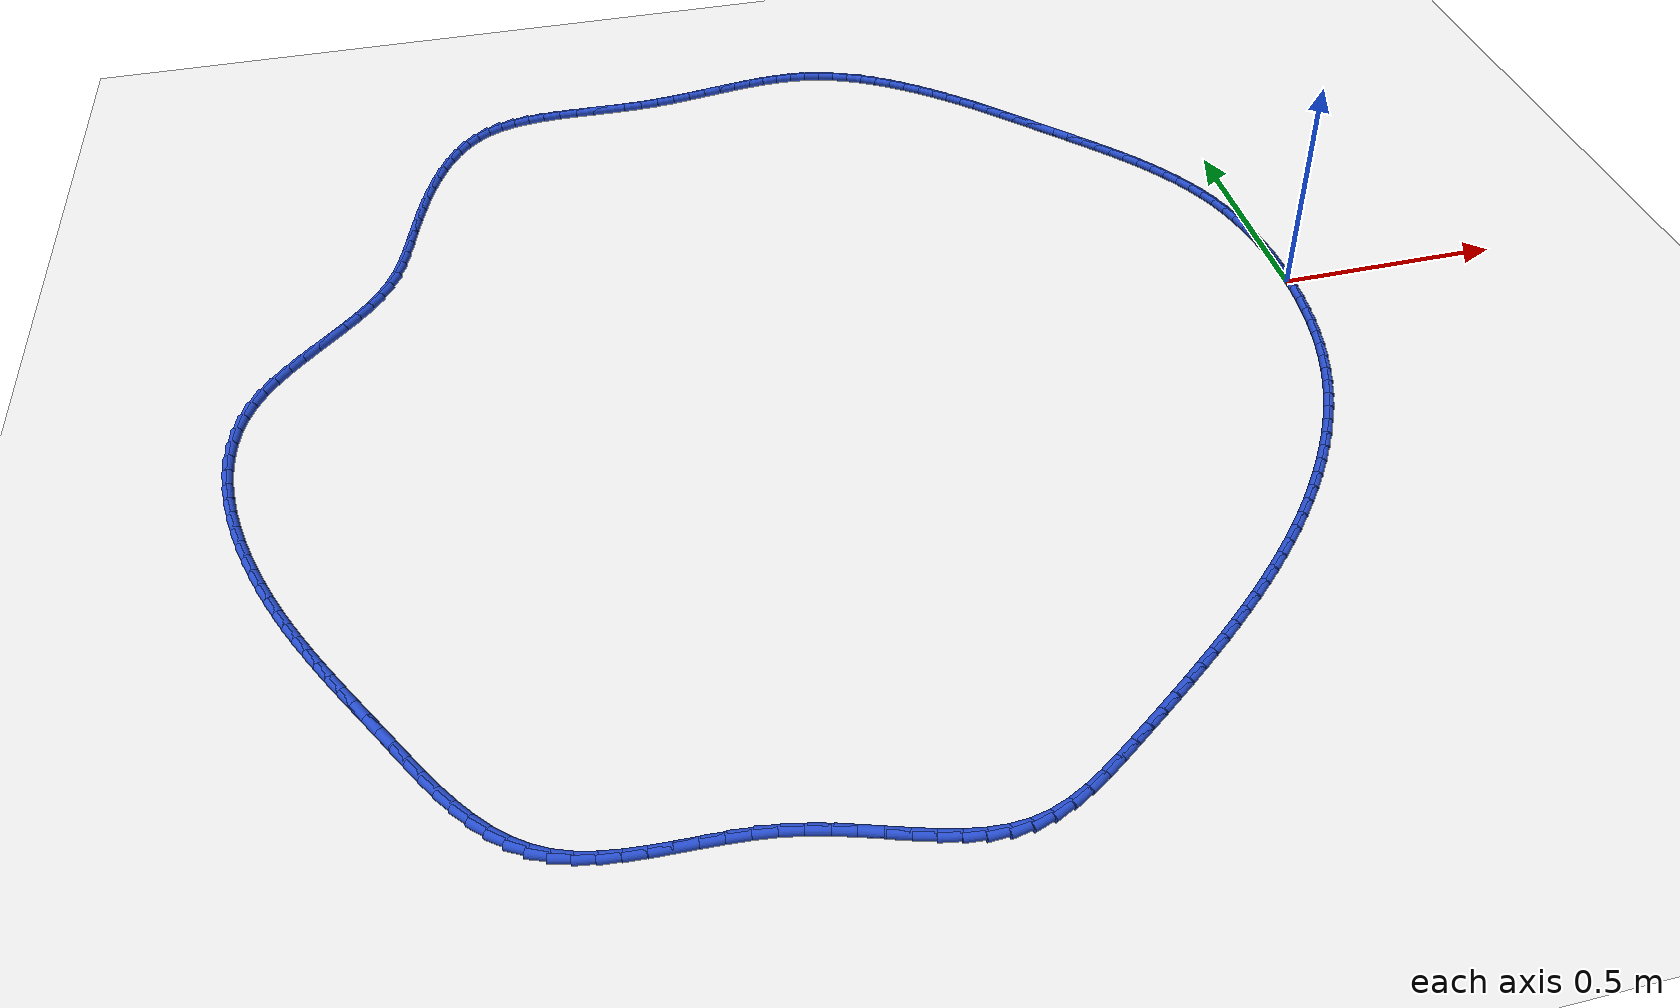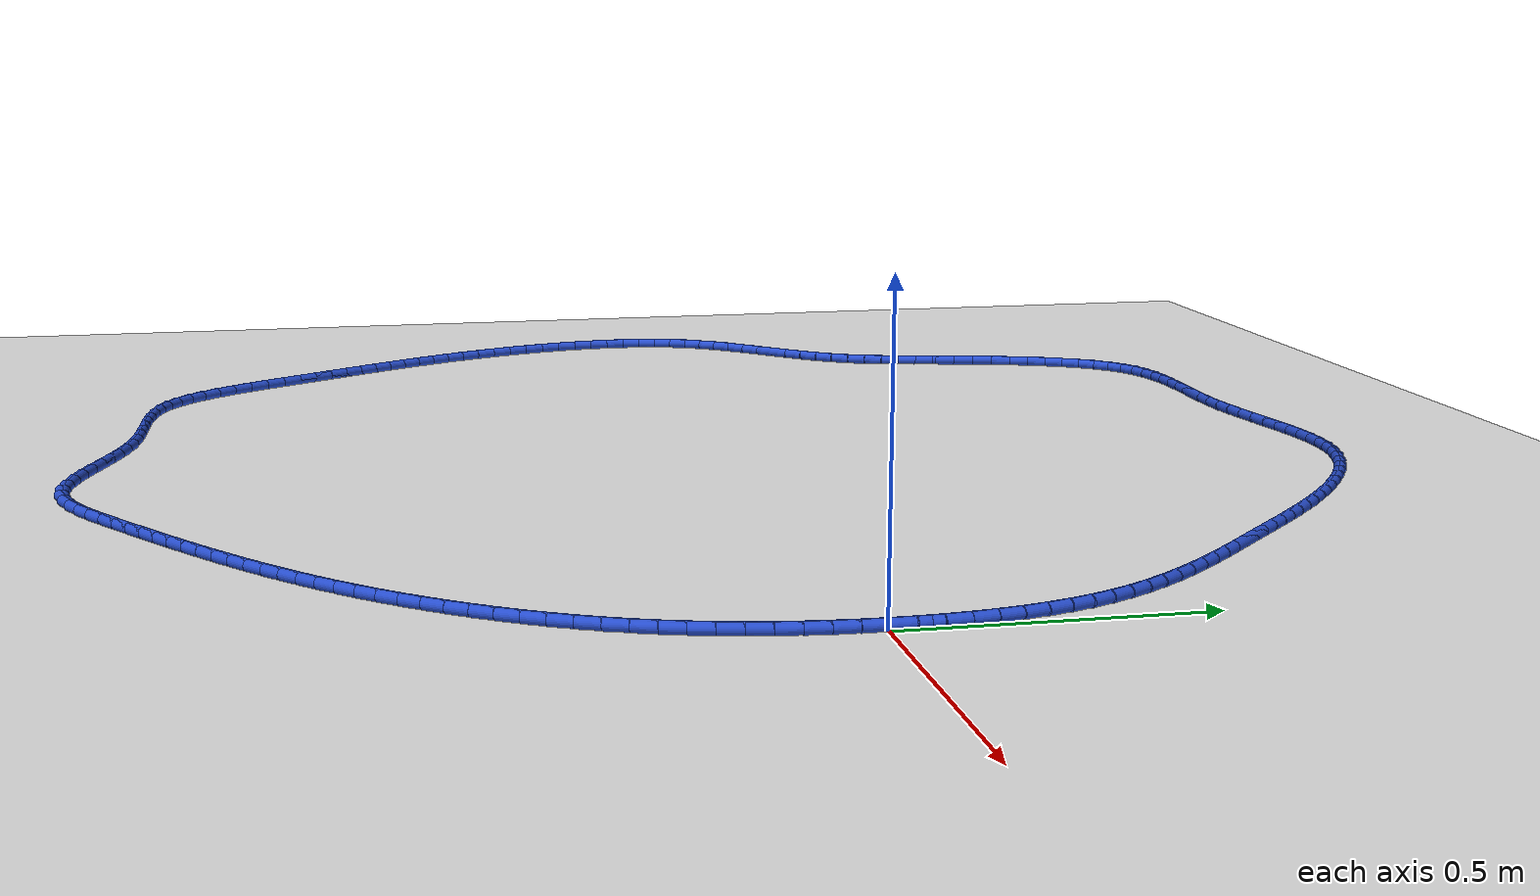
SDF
<sdf version="1.6">
 <world name="default">
  <light name="sun" type="directional">
   <pose>0 0 10 0 -0 0</pose>
   <diffuse>0.8 0.8 0.8 1</diffuse>
   <specular>0.2 0.2 0.2 1</specular>
   <attenuation>
    <range>1000</range>
    <constant>0.9</constant>
    <linear>0.01</linear>
    <quadratic>0.001</quadratic>
   </attenuation>
   <direction>-0.5 0.1 -0.9</direction>
  </light>
  <model name="ground_plane">
   <static>1</static>
   <link name="link">
    <collision name="collision">
     <geometry><plane><normal>0 0 1</normal><size>100 100</size></plane></geometry>
     <surface><friction><ode><mu>100</mu><mu2>50</mu2></ode></friction></surface>
    </collision>
    <visual name="visual">
     <cast_shadows>0</cast_shadows>
     <geometry><plane><normal>0 0 1</normal><size>100 100</size></plane></geometry>
     <material>
      <script><uri>file://media/materials/scripts/gazebo.material</uri><name>Gazebo/WhiteGlow</name></script>
     </material>
    </visual>
   </link>
  </model>
  <gravity>0 0 -9.8</gravity>
  <magnetic_field>6e-06 2.3e-05 -4.2e-05</magnetic_field>
  <atmosphere type="adiabatic"/>
  <physics name="default_physics" default="0" type="ode">
   <max_step_size>0.001</max_step_size>
   <real_time_factor>1</real_time_factor>
   <real_time_update_rate>1000</real_time_update_rate>
  </physics>
  <scene><ambient>0.4 0.4 0.4 1</ambient><background>0.7 0.7 0.7 1</background><shadows>1</shadows></scene>
  <spherical_coordinates>
   <surface_model>EARTH_WGS84</surface_model>
   <latitude_deg>0</latitude_deg>
   <longitude_deg>0</longitude_deg>
   <elevation>0</elevation>
   <heading_deg>0</heading_deg>
  </spherical_coordinates>
  <model name="line">
   <link name="link_0">
    <pose>9.540979117872439e-18 4.85722573273506e-17 0.01 0 1.57 -1.5647249568563861</pose>
    <collision name="collision">
     <geometry><cylinder><radius>0.01</radius><length>0.08</length></cylinder></geometry>
    </collision>
    <visual name="visual">
     <material>
      <script><name>Gazebo/Blue</name><uri>file://media/materials/scripts/gazebo.material</uri></script>
     </material>
     <geometry><cylinder><radius>0.01</radius><length>0.08</length></cylinder></geometry>
    </visual>
   </link>
   <link name="link_1">
    <pose>-0.00024522059150794277 0.040389167669749496 0.01 0 1.57 -1.5282353189487514</pose>
    <collision name="collision">
     <geometry><cylinder><radius>0.01</radius><length>0.08</length></cylinder></geometry>
    </collision>
    <visual name="visual">
     <material>
      <script><name>Gazebo/Blue</name><uri>file://media/materials/scripts/gazebo.material</uri></script>
     </material>
     <geometry><cylinder><radius>0.01</radius><length>0.08</length></cylinder></geometry>
    </visual>
   </link>
   <link name="link_2">
    <pose>-0.0019650079032921723 0.08077234568125619 0.01 0 1.57 -1.4888661799460283</pose>
    <collision name="collision">
     <geometry><cylinder><radius>0.01</radius><length>0.08</length></cylinder></geometry>
    </collision>
    <visual name="visual">
     <material>
      <script><name>Gazebo/Blue</name><uri>file://media/materials/scripts/gazebo.material</uri></script>
     </material>
     <geometry><cylinder><radius>0.01</radius><length>0.08</length></cylinder></geometry>
    </visual>
   </link>
   <link name="link_3">
    <pose>-0.0052689980199753655 0.1210089887397155 0.01 0 1.57 -1.4463394535777183</pose>
    <collision name="collision">
     <geometry><cylinder><radius>0.01</radius><length>0.08</length></cylinder></geometry>
    </collision>
    <visual name="visual">
     <material>
      <script><name>Gazebo/Blue</name><uri>file://media/materials/scripts/gazebo.material</uri></script>
     </material>
     <geometry><cylinder><radius>0.01</radius><length>0.08</length></cylinder></geometry>
    </visual>
   </link>
   <link name="link_4">
    <pose>-0.010266827026180234 0.16095855155032285 0.01 0 1.57 -1.4003762220411193</pose>
    <collision name="collision">
     <geometry><cylinder><radius>0.01</radius><length>0.08</length></cylinder></geometry>
    </collision>
    <visual name="visual">
     <material>
      <script><name>Gazebo/Blue</name><uri>file://media/materials/scripts/gazebo.material</uri></script>
     </material>
     <geometry><cylinder><radius>0.01</radius><length>0.08</length></cylinder></geometry>
    </visual>
   </link>
   <link name="link_5">
    <pose>-0.017068131006529465 0.20048048881827346 0.01 0 1.57 -1.3507084024429865</pose>
    <collision name="collision">
     <geometry><cylinder><radius>0.01</radius><length>0.08</length></cylinder></geometry>
    </collision>
    <visual name="visual">
     <material>
      <script><name>Gazebo/Blue</name><uri>file://media/materials/scripts/gazebo.material</uri></script>
     </material>
     <geometry><cylinder><radius>0.01</radius><length>0.08</length></cylinder></geometry>
    </visual>
   </link>
   <link name="link_6">
    <pose>-0.025782546045645748 0.23943425524876272 0.01 0 1.57 -1.2970955731137264</pose>
    <collision name="collision">
     <geometry><cylinder><radius>0.01</radius><length>0.08</length></cylinder></geometry>
    </collision>
    <visual name="visual">
     <material>
      <script><name>Gazebo/Blue</name><uri>file://media/materials/scripts/gazebo.material</uri></script>
     </material>
     <geometry><cylinder><radius>0.01</radius><length>0.08</length></cylinder></geometry>
    </visual>
   </link>
   <link name="link_7">
    <pose>-0.0365197082281518 0.27767930554698605 0.01 0 1.57 -1.2393477131960868</pose>
    <collision name="collision">
     <geometry><cylinder><radius>0.01</radius><length>0.08</length></cylinder></geometry>
    </collision>
    <visual name="visual">
     <material>
      <script><name>Gazebo/Blue</name><uri>file://media/materials/scripts/gazebo.material</uri></script>
     </material>
     <geometry><cylinder><radius>0.01</radius><length>0.08</length></cylinder></geometry>
    </visual>
   </link>
   <link name="link_8">
    <pose>-0.04938925363867031 0.31507509441813863 0.01 0 1.57 -1.1773845088528174</pose>
    <collision name="collision">
     <geometry><cylinder><radius>0.01</radius><length>0.08</length></cylinder></geometry>
    </collision>
    <visual name="visual">
     <material>
      <script><name>Gazebo/Blue</name><uri>file://media/materials/scripts/gazebo.material</uri></script>
     </material>
     <geometry><cylinder><radius>0.01</radius><length>0.08</length></cylinder></geometry>
    </visual>
   </link>
   <link name="link_9">
    <pose>-0.06449979524098105 0.35148175419750055 0.01 0 1.57 -1.114518073751251</pose>
    <collision name="collision">
     <geometry><cylinder><radius>0.01</radius><length>0.08</length></cylinder></geometry>
    </collision>
    <visual name="visual">
     <material>
      <script><name>Gazebo/Blue</name><uri>file://media/materials/scripts/gazebo.material</uri></script>
     </material>
     <geometry><cylinder><radius>0.01</radius><length>0.08</length></cylinder></geometry>
    </visual>
   </link>
   <link name="link_10">
    <pose>-0.08185044378320158 0.38683194237335117 0.01 0 1.57 -1.0571779089966264</pose>
    <collision name="collision">
     <geometry><cylinder><radius>0.01</radius><length>0.08</length></cylinder></geometry>
    </collision>
    <visual name="visual">
     <material>
      <script><name>Gazebo/Blue</name><uri>file://media/materials/scripts/gazebo.material</uri></script>
     </material>
     <geometry><cylinder><radius>0.01</radius><length>0.08</length></cylinder></geometry>
    </visual>
   </link>
   <link name="link_11">
    <pose>-0.1012349259210559 0.42119434576117826 0.01 0 1.57 -1.0062442928057733</pose>
    <collision name="collision">
     <geometry><cylinder><radius>0.01</radius><length>0.08</length></cylinder></geometry>
    </collision>
    <visual name="visual">
     <material>
      <script><name>Gazebo/Blue</name><uri>file://media/materials/scripts/gazebo.material</uri></script>
     </material>
     <geometry><cylinder><radius>0.01</radius><length>0.08</length></cylinder></geometry>
    </visual>
   </link>
   <link name="link_12">
    <pose>-0.12242435695128334 0.45465262705855647 0.01 0 1.57 -0.9617375216133484</pose>
    <collision name="collision">
     <geometry><cylinder><radius>0.01</radius><length>0.08</length></cylinder></geometry>
    </collision>
    <visual name="visual">
     <material>
      <script><name>Gazebo/Blue</name><uri>file://media/materials/scripts/gazebo.material</uri></script>
     </material>
     <geometry><cylinder><radius>0.01</radius><length>0.08</length></cylinder></geometry>
    </visual>
   </link>
   <link name="link_13">
    <pose>-0.14518985217062316 0.4872904489630595 0.01 0 1.57 -0.9235560374310187</pose>
    <collision name="collision">
     <geometry><cylinder><radius>0.01</radius><length>0.08</length></cylinder></geometry>
    </collision>
    <visual name="visual">
     <material>
      <script><name>Gazebo/Blue</name><uri>file://media/materials/scripts/gazebo.material</uri></script>
     </material>
     <geometry><cylinder><radius>0.01</radius><length>0.08</length></cylinder></geometry>
    </visual>
   </link>
   <link name="link_14">
    <pose>-0.16930252687581446 0.5191914741722615 0.01 0 1.57 -0.8915318988918951</pose>
    <collision name="collision">
     <geometry><cylinder><radius>0.01</radius><length>0.08</length></cylinder></geometry>
    </collision>
    <visual name="visual">
     <material>
      <script><name>Gazebo/Blue</name><uri>file://media/materials/scripts/gazebo.material</uri></script>
     </material>
     <geometry><cylinder><radius>0.01</radius><length>0.08</length></cylinder></geometry>
    </visual>
   </link>
   <link name="link_15">
    <pose>-0.1945334963635967 0.5504393653837367 0.01 0 1.57 -0.86547544677018</pose>
    <collision name="collision">
     <geometry><cylinder><radius>0.01</radius><length>0.08</length></cylinder></geometry>
    </collision>
    <visual name="visual">
     <material>
      <script><name>Gazebo/Blue</name><uri>file://media/materials/scripts/gazebo.material</uri></script>
     </material>
     <geometry><cylinder><radius>0.01</radius><length>0.08</length></cylinder></geometry>
    </visual>
   </link>
   <link name="link_16">
    <pose>-0.22065387593070884 0.5811177852950588 0.01 0 1.57 -0.8452090604143787</pose>
    <collision name="collision">
     <geometry><cylinder><radius>0.01</radius><length>0.08</length></cylinder></geometry>
    </collision>
    <visual name="visual">
     <material>
      <script><name>Gazebo/Blue</name><uri>file://media/materials/scripts/gazebo.material</uri></script>
     </material>
     <geometry><cylinder><radius>0.01</radius><length>0.08</length></cylinder></geometry>
    </visual>
   </link>
   <link name="link_17">
    <pose>-0.24743478087389034 0.611310396603802 0.01 0 1.57 -0.8305916437296318</pose>
    <collision name="collision">
     <geometry><cylinder><radius>0.01</radius><length>0.08</length></cylinder></geometry>
    </collision>
    <visual name="visual">
     <material>
      <script><name>Gazebo/Blue</name><uri>file://media/materials/scripts/gazebo.material</uri></script>
     </material>
     <geometry><cylinder><radius>0.01</radius><length>0.08</length></cylinder></geometry>
    </visual>
   </link>
   <link name="link_18">
    <pose>-0.27464732648988033 0.6411008620075409 0.01 0 1.57 -0.8215360327385884</pose>
    <collision name="collision">
     <geometry><cylinder><radius>0.01</radius><length>0.08</length></cylinder></geometry>
    </collision>
    <visual name="visual">
     <material>
      <script><name>Gazebo/Blue</name><uri>file://media/materials/scripts/gazebo.material</uri></script>
     </material>
     <geometry><cylinder><radius>0.01</radius><length>0.08</length></cylinder></geometry>
    </visual>
   </link>
   <link name="link_19">
    <pose>-0.3020626280754181 0.6705728442038488 0.01 0 1.57 -0.8180213803895047</pose>
    <collision name="collision">
     <geometry><cylinder><radius>0.01</radius><length>0.08</length></cylinder></geometry>
    </collision>
    <visual name="visual">
     <material>
      <script><name>Gazebo/Blue</name><uri>file://media/materials/scripts/gazebo.material</uri></script>
     </material>
     <geometry><cylinder><radius>0.01</radius><length>0.08</length></cylinder></geometry>
    </visual>
   </link>
   <link name="link_20">
    <pose>-0.3294518009272429 0.6998100058903001 0.01 0 1.57 -0.8197658720694365</pose>
    <collision name="collision">
     <geometry><cylinder><radius>0.01</radius><length>0.08</length></cylinder></geometry>
    </collision>
    <visual name="visual">
     <material>
      <script><name>Gazebo/Blue</name><uri>file://media/materials/scripts/gazebo.material</uri></script>
     </material>
     <geometry><cylinder><radius>0.01</radius><length>0.08</length></cylinder></geometry>
    </visual>
   </link>
   <link name="link_21">
    <pose>-0.3566011641479202 0.7288926972162735 0.01 0 1.57 -0.8215516015948442</pose>
    <collision name="collision">
     <geometry><cylinder><radius>0.01</radius><length>0.08</length></cylinder></geometry>
    </collision>
    <visual name="visual">
     <material>
      <script><name>Gazebo/Blue</name><uri>file://media/materials/scripts/gazebo.material</uri></script>
     </material>
     <geometry><cylinder><radius>0.01</radius><length>0.08</length></cylinder></geometry>
    </visual>
   </link>
   <link name="link_22">
    <pose>-0.38353610096723917 0.757849181935656 0.01 0 1.57 -0.8191249408894448</pose>
    <collision name="collision">
     <geometry><cylinder><radius>0.01</radius><length>0.08</length></cylinder></geometry>
    </collision>
    <visual name="visual">
     <material>
      <script><name>Gazebo/Blue</name><uri>file://media/materials/scripts/gazebo.material</uri></script>
     </material>
     <geometry><cylinder><radius>0.01</radius><length>0.08</length></cylinder></geometry>
    </visual>
   </link>
   <link name="link_23">
    <pose>-0.4104721297102003 0.7866662978808416 0.01 0 1.57 -0.8123623860567155</pose>
    <collision name="collision">
     <geometry><cylinder><radius>0.01</radius><length>0.08</length></cylinder></geometry>
    </collision>
    <visual name="visual">
     <material>
      <script><name>Gazebo/Blue</name><uri>file://media/materials/scripts/gazebo.material</uri></script>
     </material>
     <geometry><cylinder><radius>0.01</radius><length>0.08</length></cylinder></geometry>
    </visual>
   </link>
   <link name="link_24">
    <pose>-0.43763002555461145 0.8153297375408501 0.01 0 1.57 -0.8013501372681472</pose>
    <collision name="collision">
     <geometry><cylinder><radius>0.01</radius><length>0.08</length></cylinder></geometry>
    </collision>
    <visual name="visual">
     <material>
      <script><name>Gazebo/Blue</name><uri>file://media/materials/scripts/gazebo.material</uri></script>
     </material>
     <geometry><cylinder><radius>0.01</radius><length>0.08</length></cylinder></geometry>
    </visual>
   </link>
   <link name="link_25">
    <pose>-0.46523056367828014 0.843825193404701 0.01 0 1.57 -0.7862679313080547</pose>
    <collision name="collision">
     <geometry><cylinder><radius>0.01</radius><length>0.08</length></cylinder></geometry>
    </collision>
    <visual name="visual">
     <material>
      <script><name>Gazebo/Blue</name><uri>file://media/materials/scripts/gazebo.material</uri></script>
     </material>
     <geometry><cylinder><radius>0.01</radius><length>0.08</length></cylinder></geometry>
    </visual>
   </link>
   <link name="link_26">
    <pose>-0.4934945192590138 0.8721383579614135 0.01 0 1.57 -0.7673857326744724</pose>
    <collision name="collision">
     <geometry><cylinder><radius>0.01</radius><length>0.08</length></cylinder></geometry>
    </collision>
    <visual name="visual">
     <material>
      <script><name>Gazebo/Blue</name><uri>file://media/materials/scripts/gazebo.material</uri></script>
     </material>
     <geometry><cylinder><radius>0.01</radius><length>0.08</length></cylinder></geometry>
    </visual>
   </link>
   <link name="link_27">
    <pose>-0.5226426181322216 0.9002548704224066 0.01 0 1.57 -0.7448752561334837</pose>
    <collision name="collision">
     <geometry><cylinder><radius>0.01</radius><length>0.08</length></cylinder></geometry>
    </collision>
    <visual name="visual">
     <material>
      <script><name>Gazebo/Blue</name><uri>file://media/materials/scripts/gazebo.material</uri></script>
     </material>
     <geometry><cylinder><radius>0.01</radius><length>0.08</length></cylinder></geometry>
    </visual>
   </link>
   <link name="link_28">
    <pose>-0.5528311490762292 0.9280907938963721 0.01 0 1.57 -0.7182880727291902</pose>
    <collision name="collision">
     <geometry><cylinder><radius>0.01</radius><length>0.08</length></cylinder></geometry>
    </collision>
    <visual name="visual">
     <material>
      <script><name>Gazebo/Blue</name><uri>file://media/materials/scripts/gazebo.material</uri></script>
     </material>
     <geometry><cylinder><radius>0.01</radius><length>0.08</length></cylinder></geometry>
    </visual>
   </link>
   <link name="link_29">
    <pose>-0.5840252637040453 0.9553558105731482 0.01 0 1.57 -0.6871795574043023</pose>
    <collision name="collision">
     <geometry><cylinder><radius>0.01</radius><length>0.08</length></cylinder></geometry>
    </collision>
    <visual name="visual">
     <material>
      <script><name>Gazebo/Blue</name><uri>file://media/materials/scripts/gazebo.material</uri></script>
     </material>
     <geometry><cylinder><radius>0.01</radius><length>0.08</length></cylinder></geometry>
    </visual>
   </link>
   <link name="link_30">
    <pose>-0.616154838600543 0.981721514326745 0.01 0 1.57 -0.6510576280369035</pose>
    <collision name="collision">
     <geometry><cylinder><radius>0.01</radius><length>0.08</length></cylinder></geometry>
    </collision>
    <visual name="visual">
     <material>
      <script><name>Gazebo/Blue</name><uri>file://media/materials/scripts/gazebo.material</uri></script>
     </material>
     <geometry><cylinder><radius>0.01</radius><length>0.08</length></cylinder></geometry>
    </visual>
   </link>
   <link name="link_31">
    <pose>-0.6491497503505952 1.0068594990311723 0.01 0 1.57 -0.6093098272326608</pose>
    <collision name="collision">
     <geometry><cylinder><radius>0.01</radius><length>0.08</length></cylinder></geometry>
    </collision>
    <visual name="visual">
     <material>
      <script><name>Gazebo/Blue</name><uri>file://media/materials/scripts/gazebo.material</uri></script>
     </material>
     <geometry><cylinder><radius>0.01</radius><length>0.08</length></cylinder></geometry>
    </visual>
   </link>
   <link name="link_32">
    <pose>-0.6829398755390755 1.0304413585604402 0.01 0 1.57 -0.5612059864204975</pose>
    <collision name="collision">
     <geometry><cylinder><radius>0.01</radius><length>0.08</length></cylinder></geometry>
    </collision>
    <visual name="visual">
     <material>
      <script><name>Gazebo/Blue</name><uri>file://media/materials/scripts/gazebo.material</uri></script>
     </material>
     <geometry><cylinder><radius>0.01</radius><length>0.08</length></cylinder></geometry>
    </visual>
   </link>
   <link name="link_33">
    <pose>-0.7174550907508572 1.0521386867885583 0.01 0 1.57 -0.5059114349440352</pose>
    <collision name="collision">
     <geometry><cylinder><radius>0.01</radius><length>0.08</length></cylinder></geometry>
    </collision>
    <visual name="visual">
     <material>
      <script><name>Gazebo/Blue</name><uri>file://media/materials/scripts/gazebo.material</uri></script>
     </material>
     <geometry><cylinder><radius>0.01</radius><length>0.08</length></cylinder></geometry>
    </visual>
   </link>
   <link name="link_34">
    <pose>-0.7526252725708127 1.0716230775895366 0.01 0 1.57 -0.44252169561352517</pose>
    <collision name="collision">
     <geometry><cylinder><radius>0.01</radius><length>0.08</length></cylinder></geometry>
    </collision>
    <visual name="visual">
     <material>
      <script><name>Gazebo/Blue</name><uri>file://media/materials/scripts/gazebo.material</uri></script>
     </material>
     <geometry><cylinder><radius>0.01</radius><length>0.08</length></cylinder></geometry>
    </visual>
   </link>
   <link name="link_35">
    <pose>-0.7883802975838159 1.0885661248373846 0.01 0 1.57 -0.37013419399323594</pose>
    <collision name="collision">
     <geometry><cylinder><radius>0.01</radius><length>0.08</length></cylinder></geometry>
    </collision>
    <visual name="visual">
     <material>
      <script><name>Gazebo/Blue</name><uri>file://media/materials/scripts/gazebo.material</uri></script>
     </material>
     <geometry><cylinder><radius>0.01</radius><length>0.08</length></cylinder></geometry>
    </visual>
   </link>
   <link name="link_36">
    <pose>-0.8246500423747395 1.102639422406113 0.01 0 1.57 -0.28797578226313353</pose>
    <collision name="collision">
     <geometry><cylinder><radius>0.01</radius><length>0.08</length></cylinder></geometry>
    </collision>
    <visual name="visual">
     <material>
      <script><name>Gazebo/Blue</name><uri>file://media/materials/scripts/gazebo.material</uri></script>
     </material>
     <geometry><cylinder><radius>0.01</radius><length>0.08</length></cylinder></geometry>
    </visual>
   </link>
   <link name="link_37">
    <pose>-0.861364383528457 1.1135145641697306 0.01 0 1.57 -0.19571137689995918</pose>
    <collision name="collision">
     <geometry><cylinder><radius>0.01</radius><length>0.08</length></cylinder></geometry>
    </collision>
    <visual name="visual">
     <material>
      <script><name>Gazebo/Blue</name><uri>file://media/materials/scripts/gazebo.material</uri></script>
     </material>
     <geometry><cylinder><radius>0.01</radius><length>0.08</length></cylinder></geometry>
    </visual>
   </link>
   <link name="link_38">
    <pose>-0.8984537048446803 1.1208674864357258 0.01 0 1.57 -0.1015056464628421</pose>
    <collision name="collision">
     <geometry><cylinder><radius>0.01</radius><length>0.08</length></cylinder></geometry>
    </collision>
    <visual name="visual">
     <material>
      <script><name>Gazebo/Blue</name><uri>file://media/materials/scripts/gazebo.material</uri></script>
     </material>
     <geometry><cylinder><radius>0.01</radius><length>0.08</length></cylinder></geometry>
    </visual>
   </link>
   <link name="link_39">
    <pose>-0.9358841161064121 1.1246799874340112 0.01 0 1.57 -0.020000307486190774</pose>
    <collision name="collision">
     <geometry><cylinder><radius>0.01</radius><length>0.08</length></cylinder></geometry>
    </collision>
    <visual name="visual">
     <material>
      <script><name>Gazebo/Blue</name><uri>file://media/materials/scripts/gazebo.material</uri></script>
     </material>
     <geometry><cylinder><radius>0.01</radius><length>0.08</length></cylinder></geometry>
    </visual>
   </link>
   <link name="link_40">
    <pose>-0.973680381510958 1.125436025174752 0.01 0 1.57 0.04630639755655465</pose>
    <collision name="collision">
     <geometry><cylinder><radius>0.01</radius><length>0.08</length></cylinder></geometry>
    </collision>
    <visual name="visual">
     <material>
      <script><name>Gazebo/Blue</name><uri>file://media/materials/scripts/gazebo.material</uri></script>
     </material>
     <geometry><cylinder><radius>0.01</radius><length>0.08</length></cylinder></geometry>
    </visual>
   </link>
   <link name="link_41">
    <pose>-1.0118727145231043 1.1236662106437263 0.01 0 1.57 0.09718615228593032</pose>
    <collision name="collision">
     <geometry><cylinder><radius>0.01</radius><length>0.08</length></cylinder></geometry>
    </collision>
    <visual name="visual">
     <material>
      <script><name>Gazebo/Blue</name><uri>file://media/materials/scripts/gazebo.material</uri></script>
     </material>
     <geometry><cylinder><radius>0.01</radius><length>0.08</length></cylinder></geometry>
    </visual>
   </link>
   <link name="link_42">
    <pose>-1.0504913286076363 1.1199011548267124 0.01 0 1.57 0.13304613741664276</pose>
    <collision name="collision">
     <geometry><cylinder><radius>0.01</radius><length>0.08</length></cylinder></geometry>
    </collision>
    <visual name="visual">
     <material>
      <script><name>Gazebo/Blue</name><uri>file://media/materials/scripts/gazebo.material</uri></script>
     </material>
     <geometry><cylinder><radius>0.01</radius><length>0.08</length></cylinder></geometry>
    </visual>
   </link>
   <link name="link_43">
    <pose>-1.089566437229341 1.1146714687094894 0.01 0 1.57 0.154556804587153</pose>
    <collision name="collision">
     <geometry><cylinder><radius>0.01</radius><length>0.08</length></cylinder></geometry>
    </collision>
    <visual name="visual">
     <material>
      <script><name>Gazebo/Blue</name><uri>file://media/materials/scripts/gazebo.material</uri></script>
     </material>
     <geometry><cylinder><radius>0.01</radius><length>0.08</length></cylinder></geometry>
    </visual>
   </link>
   <link name="link_44">
    <pose>-1.1291282538530034 1.108507763277835 0.01 0 1.57 0.16241205543671208</pose>
    <collision name="collision">
     <geometry><cylinder><radius>0.01</radius><length>0.08</length></cylinder></geometry>
    </collision>
    <visual name="visual">
     <material>
      <script><name>Gazebo/Blue</name><uri>file://media/materials/scripts/gazebo.material</uri></script>
     </material>
     <geometry><cylinder><radius>0.01</radius><length>0.08</length></cylinder></geometry>
    </visual>
   </link>
   <link name="link_45">
    <pose>-1.1692069919434094 1.101940649517528 0.01 0 1.57 0.15720941610956438</pose>
    <collision name="collision">
     <geometry><cylinder><radius>0.01</radius><length>0.08</length></cylinder></geometry>
    </collision>
    <visual name="visual">
     <material>
      <script><name>Gazebo/Blue</name><uri>file://media/materials/scripts/gazebo.material</uri></script>
     </material>
     <geometry><cylinder><radius>0.01</radius><length>0.08</length></cylinder></geometry>
    </visual>
   </link>
   <link name="link_46">
    <pose>-1.2098328649653456 1.0955007384143463 0.01 0 1.57 0.1394207588908501</pose>
    <collision name="collision">
     <geometry><cylinder><radius>0.01</radius><length>0.08</length></cylinder></geometry>
    </collision>
    <visual name="visual">
     <material>
      <script><name>Gazebo/Blue</name><uri>file://media/materials/scripts/gazebo.material</uri></script>
     </material>
     <geometry><cylinder><radius>0.01</radius><length>0.08</length></cylinder></geometry>
    </visual>
   </link>
   <link name="link_47">
    <pose>-1.2510360863835972 1.0897186409540687 0.01 0 1.57 0.10942923757531463</pose>
    <collision name="collision">
     <geometry><cylinder><radius>0.01</radius><length>0.08</length></cylinder></geometry>
    </collision>
    <visual name="visual">
     <material>
      <script><name>Gazebo/Blue</name><uri>file://media/materials/scripts/gazebo.material</uri></script>
     </material>
     <geometry><cylinder><radius>0.01</radius><length>0.08</length></cylinder></geometry>
    </visual>
   </link>
   <link name="link_48">
    <pose>-1.2928468696629505 1.0851249681224733 0.01 0 1.57 0.06762300138029415</pose>
    <collision name="collision">
     <geometry><cylinder><radius>0.01</radius><length>0.08</length></cylinder></geometry>
    </collision>
    <visual name="visual">
     <material>
      <script><name>Gazebo/Blue</name><uri>file://media/materials/scripts/gazebo.material</uri></script>
     </material>
     <geometry><cylinder><radius>0.01</radius><length>0.08</length></cylinder></geometry>
    </visual>
   </link>
   <link name="link_49">
    <pose>-1.335295350699566 1.0822500909473964 0.01 0 1.57 0.02122253255573115</pose>
    <collision name="collision">
     <geometry><cylinder><radius>0.01</radius><length>0.08</length></cylinder></geometry>
    </collision>
    <visual name="visual">
     <material>
      <script><name>Gazebo/Blue</name><uri>file://media/materials/scripts/gazebo.material</uri></script>
     </material>
     <geometry><cylinder><radius>0.01</radius><length>0.08</length></cylinder></geometry>
    </visual>
   </link>
   <link name="link_50">
    <pose>-1.378318731035652 1.0813368887526016 0.01 0 1.57 -0.010322235732062885</pose>
    <collision name="collision">
     <geometry><cylinder><radius>0.01</radius><length>0.08</length></cylinder></geometry>
    </collision>
    <visual name="visual">
     <material>
      <script><name>Gazebo/Blue</name><uri>file://media/materials/scripts/gazebo.material</uri></script>
     </material>
     <geometry><cylinder><radius>0.01</radius><length>0.08</length></cylinder></geometry>
    </visual>
   </link>
   <link name="link_51">
    <pose>-1.421581131992768 1.0817834693145658 0.01 0 1.57 -0.024350471237909153</pose>
    <collision name="collision">
     <geometry><cylinder><radius>0.01</radius><length>0.08</length></cylinder></geometry>
    </collision>
    <visual name="visual">
     <material>
      <script><name>Gazebo/Blue</name><uri>file://media/materials/scripts/gazebo.material</uri></script>
     </material>
     <geometry><cylinder><radius>0.01</radius><length>0.08</length></cylinder></geometry>
    </visual>
   </link>
   <link name="link_52">
    <pose>-1.4646967709657177 1.0828335629989094 0.01 0 1.57 -0.021069497140108945</pose>
    <collision name="collision">
     <geometry><cylinder><radius>0.01</radius><length>0.08</length></cylinder></geometry>
    </collision>
    <visual name="visual">
     <material>
      <script><name>Gazebo/Blue</name><uri>file://media/materials/scripts/gazebo.material</uri></script>
     </material>
     <geometry><cylinder><radius>0.01</radius><length>0.08</length></cylinder></geometry>
    </visual>
   </link>
   <link name="link_53">
    <pose>-1.5072798653493038 1.0837309001712534 0.01 0 1.57 0.00028054815895689066</pose>
    <collision name="collision">
     <geometry><cylinder><radius>0.01</radius><length>0.08</length></cylinder></geometry>
    </collision>
    <visual name="visual">
     <material>
      <script><name>Gazebo/Blue</name><uri>file://media/materials/scripts/gazebo.material</uri></script>
     </material>
     <geometry><cylinder><radius>0.01</radius><length>0.08</length></cylinder></geometry>
    </visual>
   </link>
   <link name="link_54">
    <pose>-1.5489446325383305 1.0837192111972185 0.01 0 1.57 0.04152610021821178</pose>
    <collision name="collision">
     <geometry><cylinder><radius>0.01</radius><length>0.08</length></cylinder></geometry>
    </collision>
    <visual name="visual">
     <material>
      <script><name>Gazebo/Blue</name><uri>file://media/materials/scripts/gazebo.material</uri></script>
     </material>
     <geometry><cylinder><radius>0.01</radius><length>0.08</length></cylinder></geometry>
    </visual>
   </link>
   <link name="link_55">
    <pose>-1.5893052899276021 1.0820422264424252 0.01 0 1.57 0.1055915617162553</pose>
    <collision name="collision">
     <geometry><cylinder><radius>0.01</radius><length>0.08</length></cylinder></geometry>
    </collision>
    <visual name="visual">
     <material>
      <script><name>Gazebo/Blue</name><uri>file://media/materials/scripts/gazebo.material</uri></script>
     </material>
     <geometry><cylinder><radius>0.01</radius><length>0.08</length></cylinder></geometry>
    </visual>
   </link>
   <link name="link_56">
    <pose>-1.6279760549119218 1.077943676272494 0.01 0 1.57 0.19627513024860932</pose>
    <collision name="collision">
     <geometry><cylinder><radius>0.01</radius><length>0.08</length></cylinder></geometry>
    </collision>
    <visual name="visual">
     <material>
      <script><name>Gazebo/Blue</name><uri>file://media/materials/scripts/gazebo.material</uri></script>
     </material>
     <geometry><cylinder><radius>0.01</radius><length>0.08</length></cylinder></geometry>
    </visual>
   </link>
   <link name="link_57">
    <pose>-1.6645711448860934 1.070667291053046 0.01 0 1.57 0.3173305803779513</pose>
    <collision name="collision">
     <geometry><cylinder><radius>0.01</radius><length>0.08</length></cylinder></geometry>
    </collision>
    <visual name="visual">
     <material>
      <script><name>Gazebo/Blue</name><uri>file://media/materials/scripts/gazebo.material</uri></script>
     </material>
     <geometry><cylinder><radius>0.01</radius><length>0.08</length></cylinder></geometry>
    </visual>
   </link>
   <link name="link_58">
    <pose>-1.698704777244921 1.0594568011497014 0.01 0 1.57 0.4702119670649027</pose>
    <collision name="collision">
     <geometry><cylinder><radius>0.01</radius><length>0.08</length></cylinder></geometry>
    </collision>
    <visual name="visual">
     <material>
      <script><name>Gazebo/Blue</name><uri>file://media/materials/scripts/gazebo.material</uri></script>
     </material>
     <geometry><cylinder><radius>0.01</radius><length>0.08</length></cylinder></geometry>
    </visual>
   </link>
   <link name="link_59">
    <pose>-1.7299912067844978 1.0435560181376553 0.01 0 1.57 0.6420619854397065</pose>
    <collision name="collision">
     <geometry><cylinder><radius>0.01</radius><length>0.08</length></cylinder></geometry>
    </collision>
    <visual name="visual">
     <material>
      <script><name>Gazebo/Blue</name><uri>file://media/materials/scripts/gazebo.material</uri></script>
     </material>
     <geometry><cylinder><radius>0.01</radius><length>0.08</length></cylinder></geometry>
    </visual>
   </link>
   <link name="link_60">
    <pose>-1.7581714988534767 1.0224840978654735 0.01 0 1.57 0.7973124822597307</pose>
    <collision name="collision">
     <geometry><cylinder><radius>0.01</radius><length>0.08</length></cylinder></geometry>
    </collision>
    <visual name="visual">
     <material>
      <script><name>Gazebo/Blue</name><uri>file://media/materials/scripts/gazebo.material</uri></script>
     </material>
     <geometry><cylinder><radius>0.01</radius><length>0.08</length></cylinder></geometry>
    </visual>
   </link>
   <link name="link_61">
    <pose>-1.783396746167659 0.9966504902873069 0.01 0 1.57 0.9273093266484324</pose>
    <collision name="collision">
     <geometry><cylinder><radius>0.01</radius><length>0.08</length></cylinder></geometry>
    </collision>
    <visual name="visual">
     <material>
      <script><name>Gazebo/Blue</name><uri>file://media/materials/scripts/gazebo.material</uri></script>
     </material>
     <geometry><cylinder><radius>0.01</radius><length>0.08</length></cylinder></geometry>
    </visual>
   </link>
   <link name="link_62">
    <pose>-1.8059007611545972 0.9666442550070218 0.01 0 1.57 1.0333875117511162</pose>
    <collision name="collision">
     <geometry><cylinder><radius>0.01</radius><length>0.08</length></cylinder></geometry>
    </collision>
    <visual name="visual">
     <material>
      <script><name>Gazebo/Blue</name><uri>file://media/materials/scripts/gazebo.material</uri></script>
     </material>
     <geometry><cylinder><radius>0.01</radius><length>0.08</length></cylinder></geometry>
    </visual>
   </link>
   <link name="link_63">
    <pose>-1.8259173562418434 0.9330544516284861 0.01 0 1.57 1.1187870121404961</pose>
    <collision name="collision">
     <geometry><cylinder><radius>0.01</radius><length>0.08</length></cylinder></geometry>
    </collision>
    <visual name="visual">
     <material>
      <script><name>Gazebo/Blue</name><uri>file://media/materials/scripts/gazebo.material</uri></script>
     </material>
     <geometry><cylinder><radius>0.01</radius><length>0.08</length></cylinder></geometry>
    </visual>
   </link>
   <link name="link_64">
    <pose>-1.8436803438569498 0.8964701397555677 0.01 0 1.57 1.1870376339425062</pose>
    <collision name="collision">
     <geometry><cylinder><radius>0.01</radius><length>0.08</length></cylinder></geometry>
    </collision>
    <visual name="visual">
     <material>
      <script><name>Gazebo/Blue</name><uri>file://media/materials/scripts/gazebo.material</uri></script>
     </material>
     <geometry><cylinder><radius>0.01</radius><length>0.08</length></cylinder></geometry>
    </visual>
   </link>
   <link name="link_65">
    <pose>-1.8594235364274692 0.8574803789921341 0.01 0 1.57 1.2412331016380833</pose>
    <collision name="collision">
     <geometry><cylinder><radius>0.01</radius><length>0.08</length></cylinder></geometry>
    </collision>
    <visual name="visual">
     <material>
      <script><name>Gazebo/Blue</name><uri>file://media/materials/scripts/gazebo.material</uri></script>
     </material>
     <geometry><cylinder><radius>0.01</radius><length>0.08</length></cylinder></geometry>
    </visual>
   </link>
   <link name="link_66">
    <pose>-1.873380746380953 0.8166742289420519 0.01 0 1.57 1.2838199786383757</pose>
    <collision name="collision">
     <geometry><cylinder><radius>0.01</radius><length>0.08</length></cylinder></geometry>
    </collision>
    <visual name="visual">
     <material>
      <script><name>Gazebo/Blue</name><uri>file://media/materials/scripts/gazebo.material</uri></script>
     </material>
     <geometry><cylinder><radius>0.01</radius><length>0.08</length></cylinder></geometry>
    </visual>
   </link>
   <link name="link_67">
    <pose>-1.8857857861449558 0.7746407492091901 0.01 0 1.57 1.3166032890664665</pose>
    <collision name="collision">
     <geometry><cylinder><radius>0.01</radius><length>0.08</length></cylinder></geometry>
    </collision>
    <visual name="visual">
     <material>
      <script><name>Gazebo/Blue</name><uri>file://media/materials/scripts/gazebo.material</uri></script>
     </material>
     <geometry><cylinder><radius>0.01</radius><length>0.08</length></cylinder></geometry>
    </visual>
   </link>
   <link name="link_68">
    <pose>-1.8968724681470273 0.731968999397415 0.01 0 1.57 1.3408116967962602</pose>
    <collision name="collision">
     <geometry><cylinder><radius>0.01</radius><length>0.08</length></cylinder></geometry>
    </collision>
    <visual name="visual">
     <material>
      <script><name>Gazebo/Blue</name><uri>file://media/materials/scripts/gazebo.material</uri></script>
     </material>
     <geometry><cylinder><radius>0.01</radius><length>0.08</length></cylinder></geometry>
    </visual>
   </link>
   <link name="link_69">
    <pose>-1.9068746048147216 0.6892480391105942 0.01 0 1.57 1.357152278588674</pose>
    <collision name="collision">
     <geometry><cylinder><radius>0.01</radius><length>0.08</length></cylinder></geometry>
    </collision>
    <visual name="visual">
     <material>
      <script><name>Gazebo/Blue</name><uri>file://media/materials/scripts/gazebo.material</uri></script>
     </material>
     <geometry><cylinder><radius>0.01</radius><length>0.08</length></cylinder></geometry>
    </visual>
   </link>
   <link name="link_70">
    <pose>-1.9160260085755907 0.647066927952596 0.01 0 1.57 1.363798926856791</pose>
    <collision name="collision">
     <geometry><cylinder><radius>0.01</radius><length>0.08</length></cylinder></geometry>
    </collision>
    <visual name="visual">
     <material>
      <script><name>Gazebo/Blue</name><uri>file://media/materials/scripts/gazebo.material</uri></script>
     </material>
     <geometry><cylinder><radius>0.01</radius><length>0.08</length></cylinder></geometry>
    </visual>
   </link>
   <link name="link_71">
    <pose>-1.9246632632454446 0.6059382083189199 0.01 0 1.57 1.3515918358280512</pose>
    <collision name="collision">
     <geometry><cylinder><radius>0.01</radius><length>0.08</length></cylinder></geometry>
    </collision>
    <visual name="visual">
     <material>
      <script><name>Gazebo/Blue</name><uri>file://media/materials/scripts/gazebo.material</uri></script>
     </material>
     <geometry><cylinder><radius>0.01</radius><length>0.08</length></cylinder></geometry>
    </visual>
   </link>
   <link name="link_72">
    <pose>-1.9335479472331443 0.5660579979621484 0.01 0 1.57 1.3166953159096941</pose>
    <collision name="collision">
     <geometry><cylinder><radius>0.01</radius><length>0.08</length></cylinder></geometry>
    </collision>
    <visual name="visual">
     <material>
      <script><name>Gazebo/Blue</name><uri>file://media/materials/scripts/gazebo.material</uri></script>
     </material>
     <geometry><cylinder><radius>0.01</radius><length>0.08</length></cylinder></geometry>
    </visual>
   </link>
   <link name="link_73">
    <pose>-1.9435514817050845 0.5275406325230502 0.01 0 1.57 1.2576454197118017</pose>
    <collision name="collision">
     <geometry><cylinder><radius>0.01</radius><length>0.08</length></cylinder></geometry>
    </collision>
    <visual name="visual">
     <material>
      <script><name>Gazebo/Blue</name><uri>file://media/materials/scripts/gazebo.material</uri></script>
     </material>
     <geometry><cylinder><radius>0.01</radius><length>0.08</length></cylinder></geometry>
    </visual>
   </link>
   <link name="link_74">
    <pose>-1.9555452879726365 0.49050044753445127 0.01 0 1.57 1.1739585295162</pose>
    <collision name="collision">
     <geometry><cylinder><radius>0.01</radius><length>0.08</length></cylinder></geometry>
    </collision>
    <visual name="visual">
     <material>
      <script><name>Gazebo/Blue</name><uri>file://media/materials/scripts/gazebo.material</uri></script>
     </material>
     <geometry><cylinder><radius>0.01</radius><length>0.08</length></cylinder></geometry>
    </visual>
   </link>
   <link name="link_75">
    <pose>-1.9704007873471718 0.4550517785291789 0.01 0 1.57 1.0688780724815228</pose>
    <collision name="collision">
     <geometry><cylinder><radius>0.01</radius><length>0.08</length></cylinder></geometry>
    </collision>
    <visual name="visual">
     <material>
      <script><name>Gazebo/Blue</name><uri>file://media/materials/scripts/gazebo.material</uri></script>
     </material>
     <geometry><cylinder><radius>0.01</radius><length>0.08</length></cylinder></geometry>
    </visual>
   </link>
   <link name="link_76">
    <pose>-1.9889279495957357 0.4212921171947985 0.01 0 1.57 0.9695393036324064</pose>
    <collision name="collision">
     <geometry><cylinder><radius>0.01</radius><length>0.08</length></cylinder></geometry>
    </collision>
    <visual name="visual">
     <material>
      <script><name>Gazebo/Blue</name><uri>file://media/materials/scripts/gazebo.material</uri></script>
     </material>
     <geometry><cylinder><radius>0.01</radius><length>0.08</length></cylinder></geometry>
    </visual>
   </link>
   <link name="link_77">
    <pose>-2.011031273356153 0.3890707659218321 0.01 0 1.57 0.8945677628510066</pose>
    <collision name="collision">
     <geometry><cylinder><radius>0.01</radius><length>0.08</length></cylinder></geometry>
    </collision>
    <visual name="visual">
     <material>
      <script><name>Gazebo/Blue</name><uri>file://media/materials/scripts/gazebo.material</uri></script>
     </material>
     <geometry><cylinder><radius>0.01</radius><length>0.08</length></cylinder></geometry>
    </visual>
   </link>
   <link name="link_78">
    <pose>-2.0359253284623167 0.3580479178743113 0.01 0 1.57 0.8429478242038203</pose>
    <collision name="collision">
     <geometry><cylinder><radius>0.01</radius><length>0.08</length></cylinder></geometry>
    </collision>
    <visual name="visual">
     <material>
      <script><name>Gazebo/Blue</name><uri>file://media/materials/scripts/gazebo.material</uri></script>
     </material>
     <geometry><cylinder><radius>0.01</radius><length>0.08</length></cylinder></geometry>
    </visual>
   </link>
   <link name="link_79">
    <pose>-2.06280734294598 0.3278790128348016 0.01 0 1.57 0.8129749351180124</pose>
    <collision name="collision">
     <geometry><cylinder><radius>0.01</radius><length>0.08</length></cylinder></geometry>
    </collision>
    <visual name="visual">
     <material>
      <script><name>Gazebo/Blue</name><uri>file://media/materials/scripts/gazebo.material</uri></script>
     </material>
     <geometry><cylinder><radius>0.01</radius><length>0.08</length></cylinder></geometry>
    </visual>
   </link>
   <link name="link_80">
    <pose>-2.0908745448388983 0.2982194905858689 0.01 0 1.57 0.8034321846333383</pose>
    <collision name="collision">
     <geometry><cylinder><radius>0.01</radius><length>0.08</length></cylinder></geometry>
    </collision>
    <visual name="visual">
     <material>
      <script><name>Gazebo/Blue</name><uri>file://media/materials/scripts/gazebo.material</uri></script>
     </material>
     <geometry><cylinder><radius>0.01</radius><length>0.08</length></cylinder></geometry>
    </visual>
   </link>
   <link name="link_81">
    <pose>-2.119324162172823 0.2687247909100794 0.01 0 1.57 0.8139012059407257</pose>
    <collision name="collision">
     <geometry><cylinder><radius>0.01</radius><length>0.08</length></cylinder></geometry>
    </collision>
    <visual name="visual">
     <material>
      <script><name>Gazebo/Blue</name><uri>file://media/materials/scripts/gazebo.material</uri></script>
     </material>
     <geometry><cylinder><radius>0.01</radius><length>0.08</length></cylinder></geometry>
    </visual>
   </link>
   <link name="link_82">
    <pose>-2.1473534229795086 0.23905035358999882 0.01 0 1.57 0.8448423132789286</pose>
    <collision name="collision">
     <geometry><cylinder><radius>0.01</radius><length>0.08</length></cylinder></geometry>
    </collision>
    <visual name="visual">
     <material>
      <script><name>Gazebo/Blue</name><uri>file://media/materials/scripts/gazebo.material</uri></script>
     </material>
     <geometry><cylinder><radius>0.01</radius><length>0.08</length></cylinder></geometry>
    </visual>
   </link>
   <link name="link_83">
    <pose>-2.174159555290707 0.2088516184081927 0.01 0 1.57 0.8975063597841442</pose>
    <collision name="collision">
     <geometry><cylinder><radius>0.01</radius><length>0.08</length></cylinder></geometry>
    </collision>
    <visual name="visual">
     <material>
      <script><name>Gazebo/Blue</name><uri>file://media/materials/scripts/gazebo.material</uri></script>
     </material>
     <geometry><cylinder><radius>0.01</radius><length>0.08</length></cylinder></geometry>
    </visual>
   </link>
   <link name="link_84">
    <pose>-2.1989397871381726 0.17778402514722758 0.01 0 1.57 0.9736096798099205</pose>
    <collision name="collision">
     <geometry><cylinder><radius>0.01</radius><length>0.08</length></cylinder></geometry>
    </collision>
    <visual name="visual">
     <material>
      <script><name>Gazebo/Blue</name><uri>file://media/materials/scripts/gazebo.material</uri></script>
     </material>
     <geometry><cylinder><radius>0.01</radius><length>0.08</length></cylinder></geometry>
    </visual>
   </link>
   <link name="link_85">
    <pose>-2.220891346553659 0.14550301358966877 0.01 0 1.57 1.0745745067544135</pose>
    <collision name="collision">
     <geometry><cylinder><radius>0.01</radius><length>0.08</length></cylinder></geometry>
    </collision>
    <visual name="visual">
     <material>
      <script><name>Gazebo/Blue</name><uri>file://media/materials/scripts/gazebo.material</uri></script>
     </material>
     <geometry><cylinder><radius>0.01</radius><length>0.08</length></cylinder></geometry>
    </visual>
   </link>
   <link name="link_86">
    <pose>-2.2392118815751187 0.1116642535691274 0.01 0 1.57 1.1925212594301198</pose>
    <collision name="collision">
     <geometry><cylinder><radius>0.01</radius><length>0.08</length></cylinder></geometry>
    </collision>
    <visual name="visual">
     <material>
      <script><name>Gazebo/Blue</name><uri>file://media/materials/scripts/gazebo.material</uri></script>
     </material>
     <geometry><cylinder><radius>0.01</radius><length>0.08</length></cylinder></geometry>
    </visual>
   </link>
   <link name="link_87">
    <pose>-2.2533591671437074 0.0760658948776545 0.01 0 1.57 1.3046361906210342</pose>
    <collision name="collision">
     <geometry><cylinder><radius>0.01</radius><length>0.08</length></cylinder></geometry>
    </collision>
    <visual name="visual">
     <material>
      <script><name>Gazebo/Blue</name><uri>file://media/materials/scripts/gazebo.material</uri></script>
     </material>
     <geometry><cylinder><radius>0.01</radius><length>0.08</length></cylinder></geometry>
    </visual>
   </link>
   <link name="link_88">
    <pose>-2.263494053612155 0.03889118455863342 0.01 0 1.57 1.4060591646569658</pose>
    <collision name="collision">
     <geometry><cylinder><radius>0.01</radius><length>0.08</length></cylinder></geometry>
    </collision>
    <visual name="visual">
     <material>
      <script><name>Gazebo/Blue</name><uri>file://media/materials/scripts/gazebo.material</uri></script>
     </material>
     <geometry><cylinder><radius>0.01</radius><length>0.08</length></cylinder></geometry>
    </visual>
   </link>
   <link name="link_89">
    <pose>-2.2698950024406725 0.00038778908112169826 0.01 0 1.57 1.4965232953270189</pose>
    <collision name="collision">
     <geometry><cylinder><radius>0.01</radius><length>0.08</length></cylinder></geometry>
    </collision>
    <visual name="visual">
     <material>
      <script><name>Gazebo/Blue</name><uri>file://media/materials/scripts/gazebo.material</uri></script>
     </material>
     <geometry><cylinder><radius>0.01</radius><length>0.08</length></cylinder></geometry>
    </visual>
   </link>
   <link name="link_90">
    <pose>-2.2728404750894744 -0.039196625085824235 0.01 0 1.57 -1.5650676693623995</pose>
    <collision name="collision">
     <geometry><cylinder><radius>0.01</radius><length>0.08</length></cylinder></geometry>
    </collision>
    <visual name="visual">
     <material>
      <script><name>Gazebo/Blue</name><uri>file://media/materials/scripts/gazebo.material</uri></script>
     </material>
     <geometry><cylinder><radius>0.01</radius><length>0.08</length></cylinder></geometry>
    </visual>
   </link>
   <link name="link_91">
    <pose>-2.2726089330187706 -0.07961439147314757 0.01 0 1.57 -1.4946067320310474</pose>
    <collision name="collision">
     <geometry><cylinder><radius>0.01</radius><length>0.08</length></cylinder></geometry>
    </collision>
    <visual name="visual">
     <material>
      <script><name>Gazebo/Blue</name><uri>file://media/materials/scripts/gazebo.material</uri></script>
     </material>
     <geometry><cylinder><radius>0.01</radius><length>0.08</length></cylinder></geometry>
    </visual>
   </link>
   <link name="link_92">
    <pose>-2.2694788376887756 -0.12061784361179248 0.01 0 1.57 -1.4325929591205624</pose>
    <collision name="collision">
     <geometry><cylinder><radius>0.01</radius><length>0.08</length></cylinder></geometry>
    </collision>
    <visual name="visual">
     <material>
      <script><name>Gazebo/Blue</name><uri>file://media/materials/scripts/gazebo.material</uri></script>
     </material>
     <geometry><cylinder><radius>0.01</radius><length>0.08</length></cylinder></geometry>
    </visual>
   </link>
   <link name="link_93">
    <pose>-2.263728650559701 -0.16195931503270036 0.01 0 1.57 -1.3779198193536333</pose>
    <collision name="collision">
     <geometry><cylinder><radius>0.01</radius><length>0.08</length></cylinder></geometry>
    </collision>
    <visual name="visual">
     <material>
      <script><name>Gazebo/Blue</name><uri>file://media/materials/scripts/gazebo.material</uri></script>
     </material>
     <geometry><cylinder><radius>0.01</radius><length>0.08</length></cylinder></geometry>
    </visual>
   </link>
   <link name="link_94">
    <pose>-2.2556368330917604 -0.20339113926681532 0.01 0 1.57 -1.329552618511247</pose>
    <collision name="collision">
     <geometry><cylinder><radius>0.01</radius><length>0.08</length></cylinder></geometry>
    </collision>
    <visual name="visual">
     <material>
      <script><name>Gazebo/Blue</name><uri>file://media/materials/scripts/gazebo.material</uri></script>
     </material>
     <geometry><cylinder><radius>0.01</radius><length>0.08</length></cylinder></geometry>
    </visual>
   </link>
   <link name="link_95">
    <pose>-2.245481846745166 -0.24466564984508063 0.01 0 1.57 -1.2865644904491034</pose>
    <collision name="collision">
     <geometry><cylinder><radius>0.01</radius><length>0.08</length></cylinder></geometry>
    </collision>
    <visual name="visual">
     <material>
      <script><name>Gazebo/Blue</name><uri>file://media/materials/scripts/gazebo.material</uri></script>
     </material>
     <geometry><cylinder><radius>0.01</radius><length>0.08</length></cylinder></geometry>
    </visual>
   </link>
   <link name="link_96">
    <pose>-2.233542152980129 -0.2855351802984394 0.01 0 1.57 -1.2481439204090201</pose>
    <collision name="collision">
     <geometry><cylinder><radius>0.01</radius><length>0.08</length></cylinder></geometry>
    </collision>
    <visual name="visual">
     <material>
      <script><name>Gazebo/Blue</name><uri>file://media/materials/scripts/gazebo.material</uri></script>
     </material>
     <geometry><cylinder><radius>0.01</radius><length>0.08</length></cylinder></geometry>
    </visual>
   </link>
   <link name="link_97">
    <pose>-2.220096213256863 -0.325752064157835 0.01 0 1.57 -1.213587258322803</pose>
    <collision name="collision">
     <geometry><cylinder><radius>0.01</radius><length>0.08</length></cylinder></geometry>
    </collision>
    <visual name="visual">
     <material>
      <script><name>Gazebo/Blue</name><uri>file://media/materials/scripts/gazebo.material</uri></script>
     </material>
     <geometry><cylinder><radius>0.01</radius><length>0.08</length></cylinder></geometry>
    </visual>
   </link>
   <link name="link_98">
    <pose>-2.2054224890355805 -0.36506863495421116 0.01 0 1.57 -1.1822436087629875</pose>
    <collision name="collision">
     <geometry><cylinder><radius>0.01</radius><length>0.08</length></cylinder></geometry>
    </collision>
    <visual name="visual">
     <material>
      <script><name>Gazebo/Blue</name><uri>file://media/materials/scripts/gazebo.material</uri></script>
     </material>
     <geometry><cylinder><radius>0.01</radius><length>0.08</length></cylinder></geometry>
    </visual>
   </link>
   <link name="link_99">
    <pose>-2.189792791007369 -0.40324906692603985 0.01 0 1.57 -1.1530378851730145</pose>
    <collision name="collision">
     <geometry><cylinder><radius>0.01</radius><length>0.08</length></cylinder></geometry>
    </collision>
    <visual name="visual">
     <material>
      <script><name>Gazebo/Blue</name><uri>file://media/materials/scripts/gazebo.material</uri></script>
     </material>
     <geometry><cylinder><radius>0.01</radius><length>0.08</length></cylinder></geometry>
    </visual>
   </link>
   <link name="link_100">
    <pose>-2.1733600796673103 -0.44026912944980134 0.01 0 1.57 -1.1256110317099475</pose>
    <collision name="collision">
     <geometry><cylinder><radius>0.01</radius><length>0.08</length></cylinder></geometry>
    </collision>
    <visual name="visual">
     <material>
      <script><name>Gazebo/Blue</name><uri>file://media/materials/scripts/gazebo.material</uri></script>
     </material>
     <geometry><cylinder><radius>0.01</radius><length>0.08</length></cylinder></geometry>
    </visual>
   </link>
   <link name="link_101">
    <pose>-2.156174802637005 -0.47628710086149134 0.01 0 1.57 -1.1003345151985302</pose>
    <collision name="collision">
     <geometry><cylinder><radius>0.01</radius><length>0.08</length></cylinder></geometry>
    </collision>
    <visual name="visual">
     <material>
      <script><name>Gazebo/Blue</name><uri>file://media/materials/scripts/gazebo.material</uri></script>
     </material>
     <geometry><cylinder><radius>0.01</radius><length>0.08</length></cylinder></geometry>
    </visual>
   </link>
   <link name="link_102">
    <pose>-2.138284046647819 -0.5114672430634541 0.01 0 1.57 -1.0775587556066877</pose>
    <collision name="collision">
     <geometry><cylinder><radius>0.01</radius><length>0.08</length></cylinder></geometry>
    </collision>
    <visual name="visual">
     <material>
      <script><name>Gazebo/Blue</name><uri>file://media/materials/scripts/gazebo.material</uri></script>
     </material>
     <geometry><cylinder><radius>0.01</radius><length>0.08</length></cylinder></geometry>
    </visual>
   </link>
   <link name="link_103">
    <pose>-2.1197348984311155 -0.5459738179580349 0.01 0 1.57 -1.0575807448501204</pose>
    <collision name="collision">
     <geometry><cylinder><radius>0.01</radius><length>0.08</length></cylinder></geometry>
    </collision>
    <visual name="visual">
     <material>
      <script><name>Gazebo/Blue</name><uri>file://media/materials/scripts/gazebo.material</uri></script>
     </material>
     <geometry><cylinder><radius>0.01</radius><length>0.08</length></cylinder></geometry>
    </visual>
   </link>
   <link name="link_104">
    <pose>-2.1005744447182617 -0.5799710874475765 0.01 0 1.57 -1.0406357233667891</pose>
    <collision name="collision">
     <geometry><cylinder><radius>0.01</radius><length>0.08</length></cylinder></geometry>
    </collision>
    <visual name="visual">
     <material>
      <script><name>Gazebo/Blue</name><uri>file://media/materials/scripts/gazebo.material</uri></script>
     </material>
     <geometry><cylinder><radius>0.01</radius><length>0.08</length></cylinder></geometry>
    </visual>
   </link>
   <link name="link_105">
    <pose>-2.080849772240621 -0.6136233134344241 0.01 0 1.57 -1.026892623623757</pose>
    <collision name="collision">
     <geometry><cylinder><radius>0.01</radius><length>0.08</length></cylinder></geometry>
    </collision>
    <visual name="visual">
     <material>
      <script><name>Gazebo/Blue</name><uri>file://media/materials/scripts/gazebo.material</uri></script>
     </material>
     <geometry><cylinder><radius>0.01</radius><length>0.08</length></cylinder></geometry>
    </visual>
   </link>
   <link name="link_106">
    <pose>-2.0606079677295592 -0.6470947578209223 0.01 0 1.57 -1.0164529951770882</pose>
    <collision name="collision">
     <geometry><cylinder><radius>0.01</radius><length>0.08</length></cylinder></geometry>
    </collision>
    <visual name="visual">
     <material>
      <script><name>Gazebo/Blue</name><uri>file://media/materials/scripts/gazebo.material</uri></script>
     </material>
     <geometry><cylinder><radius>0.01</radius><length>0.08</length></cylinder></geometry>
    </visual>
   </link>
   <link name="link_107">
    <pose>-2.0398961179164408 -0.680549682509415 0.01 0 1.57 -1.0093528381998442</pose>
    <collision name="collision">
     <geometry><cylinder><radius>0.01</radius><length>0.08</length></cylinder></geometry>
    </collision>
    <visual name="visual">
     <material>
      <script><name>Gazebo/Blue</name><uri>file://media/materials/scripts/gazebo.material</uri></script>
     </material>
     <geometry><cylinder><radius>0.01</radius><length>0.08</length></cylinder></geometry>
    </visual>
   </link>
   <link name="link_108">
    <pose>-2.0187613095326316 -0.714152349402247 0.01 0 1.57 -1.0055666504408236</pose>
    <collision name="collision">
     <geometry><cylinder><radius>0.01</radius><length>0.08</length></cylinder></geometry>
    </collision>
    <visual name="visual">
     <material>
      <script><name>Gazebo/Blue</name><uri>file://media/materials/scripts/gazebo.material</uri></script>
     </material>
     <geometry><cylinder><radius>0.01</radius><length>0.08</length></cylinder></geometry>
    </visual>
   </link>
   <link name="link_109">
    <pose>-1.9972506293094956 -0.7480670204017632 0.01 0 1.57 -1.0050130099408847</pose>
    <collision name="collision">
     <geometry><cylinder><radius>0.01</radius><length>0.08</length></cylinder></geometry>
    </collision>
    <visual name="visual">
     <material>
      <script><name>Gazebo/Blue</name><uri>file://media/materials/scripts/gazebo.material</uri></script>
     </material>
     <geometry><cylinder><radius>0.01</radius><length>0.08</length></cylinder></geometry>
    </visual>
   </link>
   <link name="link_110">
    <pose>-1.975411163978399 -0.7824579574103071 0.01 0 1.57 -1.0074849000589137</pose>
    <collision name="collision">
     <geometry><cylinder><radius>0.01</radius><length>0.08</length></cylinder></geometry>
    </collision>
    <visual name="visual">
     <material>
      <script><name>Gazebo/Blue</name><uri>file://media/materials/scripts/gazebo.material</uri></script>
     </material>
     <geometry><cylinder><radius>0.01</radius><length>0.08</length></cylinder></geometry>
    </visual>
   </link>
   <link name="link_111">
    <pose>-1.9532887327531616 -0.8174855152771737 0.01 0 1.57 -1.0074612652439088</pose>
    <collision name="collision">
     <geometry><cylinder><radius>0.01</radius><length>0.08</length></cylinder></geometry>
    </collision>
    <visual name="visual">
     <material>
      <script><name>Gazebo/Blue</name><uri>file://media/materials/scripts/gazebo.material</uri></script>
     </material>
     <geometry><cylinder><radius>0.01</radius><length>0.08</length></cylinder></geometry>
    </visual>
   </link>
   <link name="link_112">
    <pose>-1.930838420000358 -0.8530303636802653 0.01 0 1.57 -0.9962017713672053</pose>
    <collision name="collision">
     <geometry><cylinder><radius>0.01</radius><length>0.08</length></cylinder></geometry>
    </collision>
    <visual name="visual">
     <material>
      <script><name>Gazebo/Blue</name><uri>file://media/materials/scripts/gazebo.material</uri></script>
     </material>
     <geometry><cylinder><radius>0.01</radius><length>0.08</length></cylinder></geometry>
    </visual>
   </link>
   <link name="link_113">
    <pose>-1.9078655072677977 -0.8885114133557663 0.01 0 1.57 -0.9727348324474449</pose>
    <collision name="collision">
     <geometry><cylinder><radius>0.01</radius><length>0.08</length></cylinder></geometry>
    </collision>
    <visual name="visual">
     <material>
      <script><name>Gazebo/Blue</name><uri>file://media/materials/scripts/gazebo.material</uri></script>
     </material>
     <geometry><cylinder><radius>0.01</radius><length>0.08</length></cylinder></geometry>
    </visual>
   </link>
   <link name="link_114">
    <pose>-1.8841612558986205 -0.9233043585308203 0.01 0 1.57 -0.9362641575936358</pose>
    <collision name="collision">
     <geometry><cylinder><radius>0.01</radius><length>0.08</length></cylinder></geometry>
    </collision>
    <visual name="visual">
     <material>
      <script><name>Gazebo/Blue</name><uri>file://media/materials/scripts/gazebo.material</uri></script>
     </material>
     <geometry><cylinder><radius>0.01</radius><length>0.08</length></cylinder></geometry>
    </visual>
   </link>
   <link name="link_115">
    <pose>-1.859516927235963 -0.9567848934325699 0.01 0 1.57 -0.88535998286936</pose>
    <collision name="collision">
     <geometry><cylinder><radius>0.01</radius><length>0.08</length></cylinder></geometry>
    </collision>
    <visual name="visual">
     <material>
      <script><name>Gazebo/Blue</name><uri>file://media/materials/scripts/gazebo.material</uri></script>
     </material>
     <geometry><cylinder><radius>0.01</radius><length>0.08</length></cylinder></geometry>
    </visual>
   </link>
   <link name="link_116">
    <pose>-1.8337237826229662 -0.9883287122881576 0.01 0 1.57 -0.8180248088802524</pose>
    <collision name="collision">
     <geometry><cylinder><radius>0.01</radius><length>0.08</length></cylinder></geometry>
    </collision>
    <visual name="visual">
     <material>
      <script><name>Gazebo/Blue</name><uri>file://media/materials/scripts/gazebo.material</uri></script>
     </material>
     <geometry><cylinder><radius>0.01</radius><length>0.08</length></cylinder></geometry>
    </visual>
   </link>
   <link name="link_117">
    <pose>-1.8065730834027673 -1.0173115093247265 0.01 0 1.57 -0.7318942576528683</pose>
    <collision name="collision">
     <geometry><cylinder><radius>0.01</radius><length>0.08</length></cylinder></geometry>
    </collision>
    <visual name="visual">
     <material>
      <script><name>Gazebo/Blue</name><uri>file://media/materials/scripts/gazebo.material</uri></script>
     </material>
     <geometry><cylinder><radius>0.01</radius><length>0.08</length></cylinder></geometry>
    </visual>
   </link>
   <link name="link_118">
    <pose>-1.777856090918505 -1.0431089787694194 0.01 0 1.57 -0.624747926349608</pose>
    <collision name="collision">
     <geometry><cylinder><radius>0.01</radius><length>0.08</length></cylinder></geometry>
    </collision>
    <visual name="visual">
     <material>
      <script><name>Gazebo/Blue</name><uri>file://media/materials/scripts/gazebo.material</uri></script>
     </material>
     <geometry><cylinder><radius>0.01</radius><length>0.08</length></cylinder></geometry>
    </visual>
   </link>
   <link name="link_119">
    <pose>-1.747364066513318 -1.0650968148493796 0.01 0 1.57 -0.49555046256168267</pose>
    <collision name="collision">
     <geometry><cylinder><radius>0.01</radius><length>0.08</length></cylinder></geometry>
    </collision>
    <visual name="visual">
     <material>
      <script><name>Gazebo/Blue</name><uri>file://media/materials/scripts/gazebo.material</uri></script>
     </material>
     <geometry><cylinder><radius>0.01</radius><length>0.08</length></cylinder></geometry>
    </visual>
   </link>
   <link name="link_120">
    <pose>-1.7148884201831356 -1.082651167455291 0.01 0 1.57 -0.3559049030264302</pose>
    <collision name="collision">
     <geometry><cylinder><radius>0.01</radius><length>0.08</length></cylinder></geometry>
    </collision>
    <visual name="visual">
     <material>
      <script><name>Gazebo/Blue</name><uri>file://media/materials/scripts/gazebo.material</uri></script>
     </material>
     <geometry><cylinder><radius>0.01</radius><length>0.08</length></cylinder></geometry>
    </visual>
   </link>
   <link name="link_121">
    <pose>-1.6803340985937103 -1.0954962090122429 0.01 0 1.57 -0.23785999767089555</pose>
    <collision name="collision">
     <geometry><cylinder><radius>0.01</radius><length>0.08</length></cylinder></geometry>
    </collision>
    <visual name="visual">
     <material>
      <script><name>Gazebo/Blue</name><uri>file://media/materials/scripts/gazebo.material</uri></script>
     </material>
     <geometry><cylinder><radius>0.01</radius><length>0.08</length></cylinder></geometry>
    </visual>
   </link>
   <link name="link_122">
    <pose>-1.643921914741845 -1.1043243330604793 0.01 0 1.57 -0.14815424962547968</pose>
    <collision name="collision">
     <geometry><cylinder><radius>0.01</radius><length>0.08</length></cylinder></geometry>
    </collision>
    <visual name="visual">
     <material>
      <script><name>Gazebo/Blue</name><uri>file://media/materials/scripts/gazebo.material</uri></script>
     </material>
     <geometry><cylinder><radius>0.01</radius><length>0.08</length></cylinder></geometry>
    </visual>
   </link>
   <link name="link_123">
    <pose>-1.6059271733135794 -1.109994965833926 0.01 0 1.57 -0.08560191552391141</pose>
    <collision name="collision">
     <geometry><cylinder><radius>0.01</radius><length>0.08</length></cylinder></geometry>
    </collision>
    <visual name="visual">
     <material>
      <script><name>Gazebo/Blue</name><uri>file://media/materials/scripts/gazebo.material</uri></script>
     </material>
     <geometry><cylinder><radius>0.01</radius><length>0.08</length></cylinder></geometry>
    </visual>
   </link>
   <link name="link_124">
    <pose>-1.566625178994955 -1.1133675335665127 0.01 0 1.57 -0.047911233298083965</pose>
    <collision name="collision">
     <geometry><cylinder><radius>0.01</radius><length>0.08</length></cylinder></geometry>
    </collision>
    <visual name="visual">
     <material>
      <script><name>Gazebo/Blue</name><uri>file://media/materials/scripts/gazebo.material</uri></script>
     </material>
     <geometry><cylinder><radius>0.01</radius><length>0.08</length></cylinder></geometry>
    </visual>
   </link>
   <link name="link_125">
    <pose>-1.5262912364720118 -1.1153014624921658 0.01 0 1.57 -0.03295708248124229</pose>
    <collision name="collision">
     <geometry><cylinder><radius>0.01</radius><length>0.08</length></cylinder></geometry>
    </collision>
    <visual name="visual">
     <material>
      <script><name>Gazebo/Blue</name><uri>file://media/materials/scripts/gazebo.material</uri></script>
     </material>
     <geometry><cylinder><radius>0.01</radius><length>0.08</length></cylinder></geometry>
    </visual>
   </link>
   <link name="link_126">
    <pose>-1.4852006504307897 -1.1166561788448135 0.01 0 1.57 -0.039307486964877625</pose>
    <collision name="collision">
     <geometry><cylinder><radius>0.01</radius><length>0.08</length></cylinder></geometry>
    </collision>
    <visual name="visual">
     <material>
      <script><name>Gazebo/Blue</name><uri>file://media/materials/scripts/gazebo.material</uri></script>
     </material>
     <geometry><cylinder><radius>0.01</radius><length>0.08</length></cylinder></geometry>
    </visual>
   </link>
   <link name="link_127">
    <pose>-1.4436287255573308 -1.1182911088583831 0.01 0 1.57 -0.06631490788443005</pose>
    <collision name="collision">
     <geometry><cylinder><radius>0.01</radius><length>0.08</length></cylinder></geometry>
    </collision>
    <visual name="visual">
     <material>
      <script><name>Gazebo/Blue</name><uri>file://media/materials/scripts/gazebo.material</uri></script>
     </material>
     <geometry><cylinder><radius>0.01</radius><length>0.08</length></cylinder></geometry>
    </visual>
   </link>
   <link name="link_128">
    <pose>-1.4018507665376743 -1.1210656787668025 0.01 0 1.57 -0.11395598550824884</pose>
    <collision name="collision">
     <geometry><cylinder><radius>0.01</radius><length>0.08</length></cylinder></geometry>
    </collision>
    <visual name="visual">
     <material>
      <script><name>Gazebo/Blue</name><uri>file://media/materials/scripts/gazebo.material</uri></script>
     </material>
     <geometry><cylinder><radius>0.01</radius><length>0.08</length></cylinder></geometry>
    </visual>
   </link>
   <link name="link_129">
    <pose>-1.3601420780578612 -1.1258393148039993 0.01 0 1.57 -0.18105472577503492</pose>
    <collision name="collision">
     <geometry><cylinder><radius>0.01</radius><length>0.08</length></cylinder></geometry>
    </collision>
    <visual name="visual">
     <material>
      <script><name>Gazebo/Blue</name><uri>file://media/materials/scripts/gazebo.material</uri></script>
     </material>
     <geometry><cylinder><radius>0.01</radius><length>0.08</length></cylinder></geometry>
    </visual>
   </link>
   <link name="link_130">
    <pose>-1.3187692913268476 -1.1334129918821279 0.01 0 1.57 -0.24497878687994096</pose>
    <collision name="collision">
     <geometry><cylinder><radius>0.01</radius><length>0.08</length></cylinder></geometry>
    </collision>
    <visual name="visual">
     <material>
      <script><name>Gazebo/Blue</name><uri>file://media/materials/scripts/gazebo.material</uri></script>
     </material>
     <geometry><cylinder><radius>0.01</radius><length>0.08</length></cylinder></geometry>
    </visual>
   </link>
   <link name="link_131">
    <pose>-1.2778585150324189 -1.1436406913349968 0.01 0 1.57 -0.28775071403900127</pose>
    <collision name="collision">
     <geometry><cylinder><radius>0.01</radius><length>0.08</length></cylinder></geometry>
    </collision>
    <visual name="visual">
     <material>
      <script><name>Gazebo/Blue</name><uri>file://media/materials/scripts/gazebo.material</uri></script>
     </material>
     <geometry><cylinder><radius>0.01</radius><length>0.08</length></cylinder></geometry>
    </visual>
   </link>
   <link name="link_132">
    <pose>-1.237421912105411 -1.1556085040599458 0.01 0 1.57 -0.30940194917738173</pose>
    <collision name="collision">
     <geometry><cylinder><radius>0.01</radius><length>0.08</length></cylinder></geometry>
    </collision>
    <visual name="visual">
     <material>
      <script><name>Gazebo/Blue</name><uri>file://media/materials/scripts/gazebo.material</uri></script>
     </material>
     <geometry><cylinder><radius>0.01</radius><length>0.08</length></cylinder></geometry>
    </visual>
   </link>
   <link name="link_133">
    <pose>-1.1974683606929453 -1.1683803845091592 0.01 0 1.57 -0.30998298765610044</pose>
    <collision name="collision">
     <geometry><cylinder><radius>0.01</radius><length>0.08</length></cylinder></geometry>
    </collision>
    <visual name="visual">
     <material>
      <script><name>Gazebo/Blue</name><uri>file://media/materials/scripts/gazebo.material</uri></script>
     </material>
     <geometry><cylinder><radius>0.01</radius><length>0.08</length></cylinder></geometry>
    </visual>
   </link>
   <link name="link_134">
    <pose>-1.1580067389421413 -1.1810202871348194 0.01 0 1.57 -0.2887144396331915</pose>
    <collision name="collision">
     <geometry><cylinder><radius>0.01</radius><length>0.08</length></cylinder></geometry>
    </collision>
    <visual name="visual">
     <material>
      <script><name>Gazebo/Blue</name><uri>file://media/materials/scripts/gazebo.material</uri></script>
     </material>
     <geometry><cylinder><radius>0.01</radius><length>0.08</length></cylinder></geometry>
    </visual>
   </link>
   <link name="link_135">
    <pose>-1.1190459250001203 -1.1925921663891108 0.01 0 1.57 -0.24387757959883888</pose>
    <collision name="collision">
     <geometry><cylinder><radius>0.01</radius><length>0.08</length></cylinder></geometry>
    </collision>
    <visual name="visual">
     <material>
      <script><name>Gazebo/Blue</name><uri>file://media/materials/scripts/gazebo.material</uri></script>
     </material>
     <geometry><cylinder><radius>0.01</radius><length>0.08</length></cylinder></geometry>
    </visual>
   </link>
   <link name="link_136">
    <pose>-1.0805947970140026 -1.2021599767242166 0.01 0 1.57 -0.1729770002072563</pose>
    <collision name="collision">
     <geometry><cylinder><radius>0.01</radius><length>0.08</length></cylinder></geometry>
    </collision>
    <visual name="visual">
     <material>
      <script><name>Gazebo/Blue</name><uri>file://media/materials/scripts/gazebo.material</uri></script>
     </material>
     <geometry><cylinder><radius>0.01</radius><length>0.08</length></cylinder></geometry>
    </visual>
   </link>
   <link name="link_137">
    <pose>-1.042662233130909 -1.208787672592321 0.01 0 1.57 -0.07342815125462407</pose>
    <collision name="collision">
     <geometry><cylinder><radius>0.01</radius><length>0.08</length></cylinder></geometry>
    </collision>
    <visual name="visual">
     <material>
      <script><name>Gazebo/Blue</name><uri>file://media/materials/scripts/gazebo.material</uri></script>
     </material>
     <geometry><cylinder><radius>0.01</radius><length>0.08</length></cylinder></geometry>
    </visual>
   </link>
   <link name="link_138">
    <pose>-1.0052571114979614 -1.211539208445607 0.01 0 1.57 0.05583387227103884</pose>
    <collision name="collision">
     <geometry><cylinder><radius>0.01</radius><length>0.08</length></cylinder></geometry>
    </collision>
    <visual name="visual">
     <material>
      <script><name>Gazebo/Blue</name><uri>file://media/materials/scripts/gazebo.material</uri></script>
     </material>
     <geometry><cylinder><radius>0.01</radius><length>0.08</length></cylinder></geometry>
    </visual>
   </link>
   <link name="link_139">
    <pose>-0.9683883102622799 -1.209478538736258 0.01 0 1.57 0.2099279921125532</pose>
    <collision name="collision">
     <geometry><cylinder><radius>0.01</radius><length>0.08</length></cylinder></geometry>
    </collision>
    <visual name="visual">
     <material>
      <script><name>Gazebo/Blue</name><uri>file://media/materials/scripts/gazebo.material</uri></script>
     </material>
     <geometry><cylinder><radius>0.01</radius><length>0.08</length></cylinder></geometry>
    </visual>
   </link>
   <link name="link_140">
    <pose>-0.9320630433524567 -1.2017388170487442 0.01 0 1.57 0.3533651986936958</pose>
    <collision name="collision">
     <geometry><cylinder><radius>0.01</radius><length>0.08</length></cylinder></geometry>
    </collision>
    <visual name="visual">
     <material>
      <script><name>Gazebo/Blue</name><uri>file://media/materials/scripts/gazebo.material</uri></script>
     </material>
     <geometry><cylinder><radius>0.01</radius><length>0.08</length></cylinder></geometry>
    </visual>
   </link>
   <link name="link_141">
    <pose>-0.8962625337798734 -1.1885339137650166 0.01 0 1.57 0.46235397760210983</pose>
    <collision name="collision">
     <geometry><cylinder><radius>0.01</radius><length>0.08</length></cylinder></geometry>
    </collision>
    <visual name="visual">
     <material>
      <script><name>Gazebo/Blue</name><uri>file://media/materials/scripts/gazebo.material</uri></script>
     </material>
     <geometry><cylinder><radius>0.01</radius><length>0.08</length></cylinder></geometry>
    </visual>
   </link>
   <link name="link_142">
    <pose>-0.8609474245304143 -1.1709334281766899 0.01 0 1.57 0.5400242235394976</pose>
    <collision name="collision">
     <geometry><cylinder><radius>0.01</radius><length>0.08</length></cylinder></geometry>
    </collision>
    <visual name="visual">
     <material>
      <script><name>Gazebo/Blue</name><uri>file://media/materials/scripts/gazebo.material</uri></script>
     </material>
     <geometry><cylinder><radius>0.01</radius><length>0.08</length></cylinder></geometry>
    </visual>
   </link>
   <link name="link_143">
    <pose>-0.8260777950677244 -1.150030391143689 0.01 0 1.57 0.5907397959385251</pose>
    <collision name="collision">
     <geometry><cylinder><radius>0.01</radius><length>0.08</length></cylinder></geometry>
    </collision>
    <visual name="visual">
     <material>
      <script><name>Gazebo/Blue</name><uri>file://media/materials/scripts/gazebo.material</uri></script>
     </material>
     <geometry><cylinder><radius>0.01</radius><length>0.08</length></cylinder></geometry>
    </visual>
   </link>
   <link name="link_144">
    <pose>-0.7916137248554469 -1.1269178335259364 0.01 0 1.57 0.6177793924117527</pose>
    <collision name="collision">
     <geometry><cylinder><radius>0.01</radius><length>0.08</length></cylinder></geometry>
    </collision>
    <visual name="visual">
     <material>
      <script><name>Gazebo/Blue</name><uri>file://media/materials/scripts/gazebo.material</uri></script>
     </material>
     <geometry><cylinder><radius>0.01</radius><length>0.08</length></cylinder></geometry>
    </visual>
   </link>
   <link name="link_145">
    <pose>-0.7575152933572257 -1.1026887861833563 0.01 0 1.57 0.6252822630911149</pose>
    <collision name="collision">
     <geometry><cylinder><radius>0.01</radius><length>0.08</length></cylinder></geometry>
    </collision>
    <visual name="visual">
     <material>
      <script><name>Gazebo/Blue</name><uri>file://media/materials/scripts/gazebo.material</uri></script>
     </material>
     <geometry><cylinder><radius>0.01</radius><length>0.08</length></cylinder></geometry>
    </visual>
   </link>
   <link name="link_146">
    <pose>-0.7237495372003689 -1.078312823524311 0.01 0 1.57 0.6286489795895932</pose>
    <collision name="collision">
     <geometry><cylinder><radius>0.01</radius><length>0.08</length></cylinder></geometry>
    </collision>
    <visual name="visual">
     <material>
      <script><name>Gazebo/Blue</name><uri>file://media/materials/scripts/gazebo.material</uri></script>
     </material>
     <geometry><cylinder><radius>0.01</radius><length>0.08</length></cylinder></geometry>
    </visual>
   </link>
   <link name="link_147">
    <pose>-0.690325615663957 -1.0540120439210972 0.01 0 1.57 0.6335635386000249</pose>
    <collision name="collision">
     <geometry><cylinder><radius>0.01</radius><length>0.08</length></cylinder></geometry>
    </collision>
    <visual name="visual">
     <material>
      <script><name>Gazebo/Blue</name><uri>file://media/materials/scripts/gazebo.material</uri></script>
     </material>
     <geometry><cylinder><radius>0.01</radius><length>0.08</length></cylinder></geometry>
    </visual>
   </link>
   <link name="link_148">
    <pose>-0.657268458841842 -1.0297286890509547 0.01 0 1.57 0.6400656069052517</pose>
    <collision name="collision">
     <geometry><cylinder><radius>0.01</radius><length>0.08</length></cylinder></geometry>
    </collision>
    <visual name="visual">
     <material>
      <script><name>Gazebo/Blue</name><uri>file://media/materials/scripts/gazebo.material</uri></script>
     </material>
     <geometry><cylinder><radius>0.01</radius><length>0.08</length></cylinder></geometry>
    </visual>
   </link>
   <link name="link_149">
    <pose>-0.6246030244501314 -1.0054045104279712 0.01 0 1.57 0.6481817746326342</pose>
    <collision name="collision">
     <geometry><cylinder><radius>0.01</radius><length>0.08</length></cylinder></geometry>
    </collision>
    <visual name="visual">
     <material>
      <script><name>Gazebo/Blue</name><uri>file://media/materials/scripts/gazebo.material</uri></script>
     </material>
     <geometry><cylinder><radius>0.01</radius><length>0.08</length></cylinder></geometry>
    </visual>
   </link>
   <link name="link_150">
    <pose>-0.5923542702049297 -0.9809812595662316 0.01 0 1.57 0.6579347712379185</pose>
    <collision name="collision">
     <geometry><cylinder><radius>0.01</radius><length>0.08</length></cylinder></geometry>
    </collision>
    <visual name="visual">
     <material>
      <script><name>Gazebo/Blue</name><uri>file://media/materials/scripts/gazebo.material</uri></script>
     </material>
     <geometry><cylinder><radius>0.01</radius><length>0.08</length></cylinder></geometry>
    </visual>
   </link>
   <link name="link_151">
    <pose>-0.560547153822343 -0.9564006879798228 0.01 0 1.57 0.6693426026866303</pose>
    <collision name="collision">
     <geometry><cylinder><radius>0.01</radius><length>0.08</length></cylinder></geometry>
    </collision>
    <visual name="visual">
     <material>
      <script><name>Gazebo/Blue</name><uri>file://media/materials/scripts/gazebo.material</uri></script>
     </material>
     <geometry><cylinder><radius>0.01</radius><length>0.08</length></cylinder></geometry>
    </visual>
   </link>
   <link name="link_152">
    <pose>-0.5292066330184766 -0.9316045471828301 0.01 0 1.57 0.6824175420510221</pose>
    <collision name="collision">
     <geometry><cylinder><radius>0.01</radius><length>0.08</length></cylinder></geometry>
    </collision>
    <visual name="visual">
     <material>
      <script><name>Gazebo/Blue</name><uri>file://media/materials/scripts/gazebo.material</uri></script>
     </material>
     <geometry><cylinder><radius>0.01</radius><length>0.08</length></cylinder></geometry>
    </visual>
   </link>
   <link name="link_153">
    <pose>-0.49835766550943666 -0.9065345886893399 0.01 0 1.57 0.6971649826477344</pose>
    <collision name="collision">
     <geometry><cylinder><radius>0.01</radius><length>0.08</length></cylinder></geometry>
    </collision>
    <visual name="visual">
     <material>
      <script><name>Gazebo/Blue</name><uri>file://media/materials/scripts/gazebo.material</uri></script>
     </material>
     <geometry><cylinder><radius>0.01</radius><length>0.08</length></cylinder></geometry>
    </visual>
   </link>
   <link name="link_154">
    <pose>-0.4680252090113279 -0.8811325640134373 0.01 0 1.57 0.7135821732879006</pose>
    <collision name="collision">
     <geometry><cylinder><radius>0.01</radius><length>0.08</length></cylinder></geometry>
    </collision>
    <visual name="visual">
     <material>
      <script><name>Gazebo/Blue</name><uri>file://media/materials/scripts/gazebo.material</uri></script>
     </material>
     <geometry><cylinder><radius>0.01</radius><length>0.08</length></cylinder></geometry>
    </visual>
   </link>
   <link name="link_155">
    <pose>-0.4382342212402574 -0.8553402246692094 0.01 0 1.57 0.7316568679035345</pose>
    <collision name="collision">
     <geometry><cylinder><radius>0.01</radius><length>0.08</length></cylinder></geometry>
    </collision>
    <visual name="visual">
     <material>
      <script><name>Gazebo/Blue</name><uri>file://media/materials/scripts/gazebo.material</uri></script>
     </material>
     <geometry><cylinder><radius>0.01</radius><length>0.08</length></cylinder></geometry>
    </visual>
   </link>
   <link name="link_156">
    <pose>-0.4090096599123303 -0.8290993221707421 0.01 0 1.57 0.7513659364025579</pose>
    <collision name="collision">
     <geometry><cylinder><radius>0.01</radius><length>0.08</length></cylinder></geometry>
    </collision>
    <visual name="visual">
     <material>
      <script><name>Gazebo/Blue</name><uri>file://media/materials/scripts/gazebo.material</uri></script>
     </material>
     <geometry><cylinder><radius>0.01</radius><length>0.08</length></cylinder></geometry>
    </visual>
   </link>
   <link name="link_157">
    <pose>-0.38037648274365216 -0.8023516080321208 0.01 0 1.57 0.7726739993015809</pose>
    <collision name="collision">
     <geometry><cylinder><radius>0.01</radius><length>0.08</length></cylinder></geometry>
    </collision>
    <visual name="visual">
     <material>
      <script><name>Gazebo/Blue</name><uri>file://media/materials/scripts/gazebo.material</uri></script>
     </material>
     <geometry><cylinder><radius>0.01</radius><length>0.08</length></cylinder></geometry>
    </visual>
   </link>
   <link name="link_158">
    <pose>-0.35235964745032883 -0.7750388337674322 0.01 0 1.57 0.7955321641745369</pose>
    <collision name="collision">
     <geometry><cylinder><radius>0.01</radius><length>0.08</length></cylinder></geometry>
    </collision>
    <visual name="visual">
     <material>
      <script><name>Gazebo/Blue</name><uri>file://media/materials/scripts/gazebo.material</uri></script>
     </material>
     <geometry><cylinder><radius>0.01</radius><length>0.08</length></cylinder></geometry>
    </visual>
   </link>
   <link name="link_159">
    <pose>-0.32498411174846525 -0.7471027508907611 0.01 0 1.57 0.8198769553615992</pose>
    <collision name="collision">
     <geometry><cylinder><radius>0.01</radius><length>0.08</length></cylinder></geometry>
    </collision>
    <visual name="visual">
     <material>
      <script><name>Gazebo/Blue</name><uri>file://media/materials/scripts/gazebo.material</uri></script>
     </material>
     <geometry><cylinder><radius>0.01</radius><length>0.08</length></cylinder></geometry>
    </visual>
   </link>
   <link name="link_160">
    <pose>-0.29827483335416843 -0.7184851109161949 0.01 0 1.57 0.8456295373603967</pose>
    <collision name="collision">
     <geometry><cylinder><radius>0.01</radius><length>0.08</length></cylinder></geometry>
    </collision>
    <visual name="visual">
     <material>
      <script><name>Gazebo/Blue</name><uri>file://media/materials/scripts/gazebo.material</uri></script>
     </material>
     <geometry><cylinder><radius>0.01</radius><length>0.08</length></cylinder></geometry>
    </visual>
   </link>
   <link name="link_161">
    <pose>-0.2722567699835433 -0.6891276653578191 0.01 0 1.57 0.8726953342764191</pose>
    <collision name="collision">
     <geometry><cylinder><radius>0.01</radius><length>0.08</length></cylinder></geometry>
    </collision>
    <visual name="visual">
     <material>
      <script><name>Gazebo/Blue</name><uri>file://media/materials/scripts/gazebo.material</uri></script>
     </material>
     <geometry><cylinder><radius>0.01</radius><length>0.08</length></cylinder></geometry>
    </visual>
   </link>
   <link name="link_162">
    <pose>-0.24695487935269567 -0.6589721657297196 0.01 0 1.57 0.9009665301244184</pose>
    <collision name="collision">
     <geometry><cylinder><radius>0.01</radius><length>0.08</length></cylinder></geometry>
    </collision>
    <visual name="visual">
     <material>
      <script><name>Gazebo/Blue</name><uri>file://media/materials/scripts/gazebo.material</uri></script>
     </material>
     <geometry><cylinder><radius>0.01</radius><length>0.08</length></cylinder></geometry>
    </visual>
   </link>
   <link name="link_163">
    <pose>-0.22239559700766737 -0.6279620772653204 0.01 0 1.57 0.9304281320621328</pose>
    <collision name="collision">
     <geometry><cylinder><radius>0.01</radius><length>0.08</length></cylinder></geometry>
    </collision>
    <visual name="visual">
     <material>
      <script><name>Gazebo/Blue</name><uri>file://media/materials/scripts/gazebo.material</uri></script>
     </material>
     <geometry><cylinder><radius>0.01</radius><length>0.08</length></cylinder></geometry>
    </visual>
   </link>
   <link name="link_164">
    <pose>-0.19864378235768787 -0.5960854222311491 0.01 0 1.57 0.9612385128471095</pose>
    <collision name="collision">
     <geometry><cylinder><radius>0.01</radius><length>0.08</length></cylinder></geometry>
    </collision>
    <visual name="visual">
     <material>
      <script><name>Gazebo/Blue</name><uri>file://media/materials/scripts/gazebo.material</uri></script>
     </material>
     <geometry><cylinder><radius>0.01</radius><length>0.08</length></cylinder></geometry>
    </visual>
   </link>
   <link name="link_165">
    <pose>-0.17580535629244456 -0.5633778385573408 0.01 0 1.57 0.9935454188025418</pose>
    <collision name="collision">
     <geometry><cylinder><radius>0.01</radius><length>0.08</length></cylinder></geometry>
    </collision>
    <visual name="visual">
     <material>
      <script><name>Gazebo/Blue</name><uri>file://media/materials/scripts/gazebo.material</uri></script>
     </material>
     <geometry><cylinder><radius>0.01</radius><length>0.08</length></cylinder></geometry>
    </visual>
   </link>
   <link name="link_166">
    <pose>-0.15398824578404505 -0.5298772904648663 0.01 0 1.57 1.0274939548153512</pose>
    <collision name="collision">
     <geometry><cylinder><radius>0.01</radius><length>0.08</length></cylinder></geometry>
    </collision>
    <visual name="visual">
     <material>
      <script><name>Gazebo/Blue</name><uri>file://media/materials/scripts/gazebo.material</uri></script>
     </material>
     <geometry><cylinder><radius>0.01</radius><length>0.08</length></cylinder></geometry>
    </visual>
   </link>
   <link name="link_167">
    <pose>-0.13330037780459578 -0.49562174217469507 0.01 0 1.57 1.0632284976731243</pose>
    <collision name="collision">
     <geometry><cylinder><radius>0.01</radius><length>0.08</length></cylinder></geometry>
    </collision>
    <visual name="visual">
     <material>
      <script><name>Gazebo/Blue</name><uri>file://media/materials/scripts/gazebo.material</uri></script>
     </material>
     <geometry><cylinder><radius>0.01</radius><length>0.08</length></cylinder></geometry>
    </visual>
   </link>
   <link name="link_168">
    <pose>-0.11384967932620366 -0.4606491579077971 0.01 0 1.57 1.1008904974727114</pose>
    <collision name="collision">
     <geometry><cylinder><radius>0.01</radius><length>0.08</length></cylinder></geometry>
    </collision>
    <visual name="visual">
     <material>
      <script><name>Gazebo/Blue</name><uri>file://media/materials/scripts/gazebo.material</uri></script>
     </material>
     <geometry><cylinder><radius>0.01</radius><length>0.08</length></cylinder></geometry>
    </visual>
   </link>
   <link name="link_169">
    <pose>-0.09574407732097545 -0.42499750188514224 0.01 0 1.57 1.1406152615879885</pose>
    <collision name="collision">
     <geometry><cylinder><radius>0.01</radius><length>0.08</length></cylinder></geometry>
    </collision>
    <visual name="visual">
     <material>
      <script><name>Gazebo/Blue</name><uri>file://media/materials/scripts/gazebo.material</uri></script>
     </material>
     <geometry><cylinder><radius>0.01</radius><length>0.08</length></cylinder></geometry>
    </visual>
   </link>
   <link name="link_170">
    <pose>-0.07909149876101772 -0.3887047383276996 0.01 0 1.57 1.1825275727127291</pose>
    <collision name="collision">
     <geometry><cylinder><radius>0.01</radius><length>0.08</length></cylinder></geometry>
    </collision>
    <visual name="visual">
     <material>
      <script><name>Gazebo/Blue</name><uri>file://media/materials/scripts/gazebo.material</uri></script>
     </material>
     <geometry><cylinder><radius>0.01</radius><length>0.08</length></cylinder></geometry>
    </visual>
   </link>
   <link name="link_171">
    <pose>-0.063999870618438 -0.3518088314564406 0.01 0 1.57 1.226499634315418</pose>
    <collision name="collision">
     <geometry><cylinder><radius>0.01</radius><length>0.08</length></cylinder></geometry>
    </collision>
    <visual name="visual">
     <material>
      <script><name>Gazebo/Blue</name><uri>file://media/materials/scripts/gazebo.material</uri></script>
     </material>
     <geometry><cylinder><radius>0.01</radius><length>0.08</length></cylinder></geometry>
    </visual>
   </link>
   <link name="link_172">
    <pose>-0.05056737055291623 -0.3143484254611967 0.01 0 1.57 1.2704327286751604</pose>
    <collision name="collision">
     <geometry><cylinder><radius>0.01</radius><length>0.08</length></cylinder></geometry>
    </collision>
    <visual name="visual">
     <material>
      <script><name>Gazebo/Blue</name><uri>file://media/materials/scripts/gazebo.material</uri></script>
     </material>
     <geometry><cylinder><radius>0.01</radius><length>0.08</length></cylinder></geometry>
    </visual>
   </link>
   <link name="link_173">
    <pose>-0.03880362101232436 -0.2763683408429051 0.01 0 1.57 1.3131385669383353</pose>
    <collision name="collision">
     <geometry><cylinder><radius>0.01</radius><length>0.08</length></cylinder></geometry>
    </collision>
    <visual name="visual">
     <material>
      <script><name>Gazebo/Blue</name><uri>file://media/materials/scripts/gazebo.material</uri></script>
     </material>
     <geometry><cylinder><radius>0.01</radius><length>0.08</length></cylinder></geometry>
    </visual>
   </link>
   <link name="link_174">
    <pose>-0.028671030506062015 -0.23791669105349533 0.01 0 1.57 1.3545662736095114</pose>
    <collision name="collision">
     <geometry><cylinder><radius>0.01</radius><length>0.08</length></cylinder></geometry>
    </collision>
    <visual name="visual">
     <material>
      <script><name>Gazebo/Blue</name><uri>file://media/materials/scripts/gazebo.material</uri></script>
     </material>
     <geometry><cylinder><radius>0.01</radius><length>0.08</length></cylinder></geometry>
    </visual>
   </link>
   <link name="link_175">
    <pose>-0.020131566405746888 -0.1990416203121893 0.01 0 1.57 1.3946954159127227</pose>
    <collision name="collision">
     <geometry><cylinder><radius>0.01</radius><length>0.08</length></cylinder></geometry>
    </collision>
    <visual name="visual">
     <material>
      <script><name>Gazebo/Blue</name><uri>file://media/materials/scripts/gazebo.material</uri></script>
     </material>
     <geometry><cylinder><radius>0.01</radius><length>0.08</length></cylinder></geometry>
    </visual>
   </link>
   <link name="link_176">
    <pose>-0.013147196082996589 -0.1597912728382088 0.01 0 1.57 1.433523207600298</pose>
    <collision name="collision">
     <geometry><cylinder><radius>0.01</radius><length>0.08</length></cylinder></geometry>
    </collision>
    <visual name="visual">
     <material>
      <script><name>Gazebo/Blue</name><uri>file://media/materials/scripts/gazebo.material</uri></script>
     </material>
     <geometry><cylinder><radius>0.01</radius><length>0.08</length></cylinder></geometry>
    </visual>
   </link>
   <link name="link_177">
    <pose>-0.0076798869094291166 -0.12021379285077771 0.01 0 1.57 1.4710622462772058</pose>
    <collision name="collision">
     <geometry><cylinder><radius>0.01</radius><length>0.08</length></cylinder></geometry>
    </collision>
    <visual name="visual">
     <material>
      <script><name>Gazebo/Blue</name><uri>file://media/materials/scripts/gazebo.material</uri></script>
     </material>
     <geometry><cylinder><radius>0.01</radius><length>0.08</length></cylinder></geometry>
    </visual>
   </link>
   <link name="link_178">
    <pose>-0.003691606256662039 -0.0803573245691176 0.01 0 1.57 1.5073382287950174</pose>
    <collision name="collision">
     <geometry><cylinder><radius>0.01</radius><length>0.08</length></cylinder></geometry>
    </collision>
    <visual name="visual">
     <material>
      <script><name>Gazebo/Blue</name><uri>file://media/materials/scripts/gazebo.material</uri></script>
     </material>
     <geometry><cylinder><radius>0.01</radius><length>0.08</length></cylinder></geometry>
    </visual>
   </link>
   <link name="link_179">
    <pose>-0.0011443214963130846 -0.0402700122124508 0.01 0 1.57 1.5423877523632628</pose>
    <collision name="collision">
     <geometry><cylinder><radius>0.01</radius><length>0.08</length></cylinder></geometry>
    </collision>
    <visual name="visual">
     <material>
      <script><name>Gazebo/Blue</name><uri>file://media/materials/scripts/gazebo.material</uri></script>
     </material>
     <geometry><cylinder><radius>0.01</radius><length>0.08</length></cylinder></geometry>
    </visual>
   </link>
   <link name="link_180">
    <pose>2.42861286636753e-17 2.8449465006019636e-16 0.01 0 1.57 -1.565336376128849</pose>
    <collision name="collision">
     <geometry><cylinder><radius>0.01</radius><length>0.08</length></cylinder></geometry>
    </collision>
    <visual name="visual">
     <material>
      <script><name>Gazebo/Blue</name><uri>file://media/materials/scripts/gazebo.material</uri></script>
     </material>
     <geometry><cylinder><radius>0.01</radius><length>0.08</length></cylinder></geometry>
    </visual>
   </link>
   <link name="link_181">
    <pose>-0.00022060913934043684 0.04040456784901328 0.01 0 1.57 -1.5653363761288495</pose>
    <collision name="collision">
     <geometry><cylinder><radius>0.01</radius><length>0.08</length></cylinder></geometry>
    </collision>
    <visual name="visual">
     <material>
      <script><name>Gazebo/Blue</name><uri>file://media/materials/scripts/gazebo.material</uri></script>
     </material>
     <geometry><cylinder><radius>0.01</radius><length>0.08</length></cylinder></geometry>
    </visual>
   </link>
  </model>
 </world>
</sdf>
